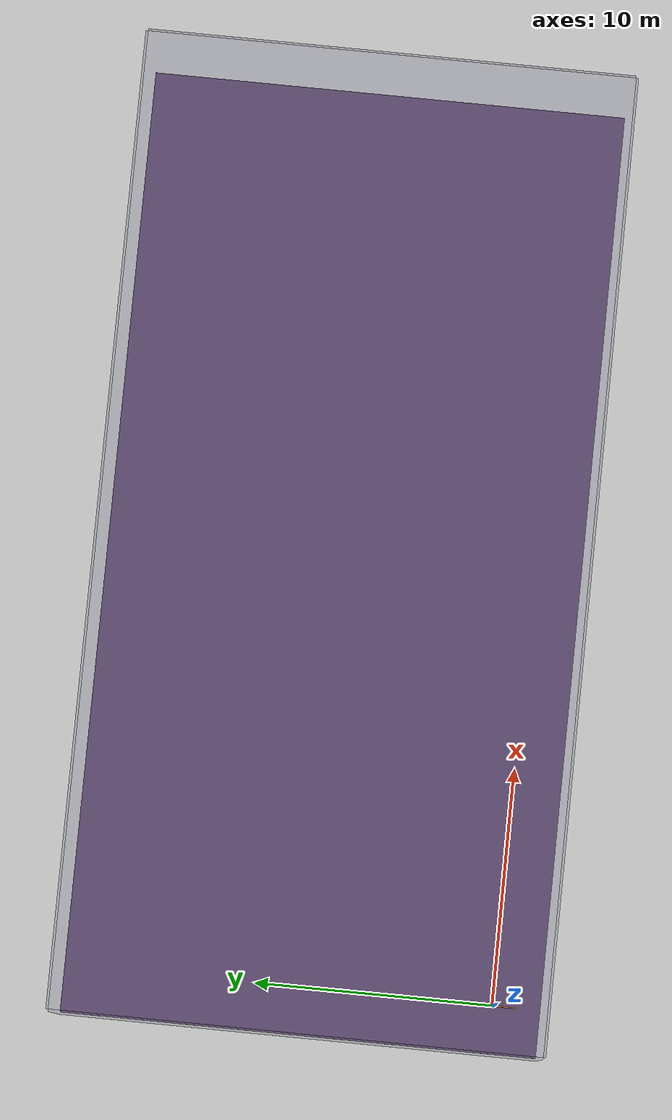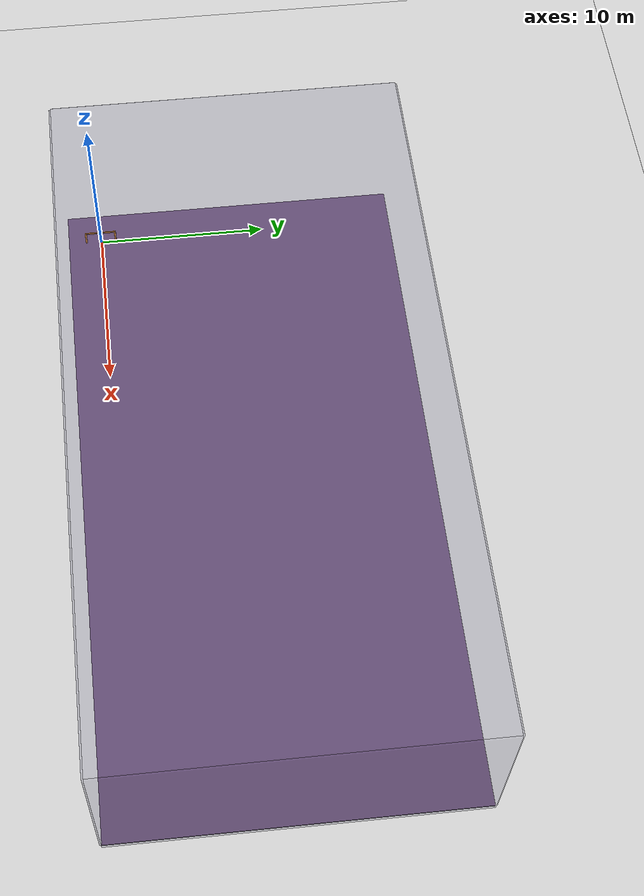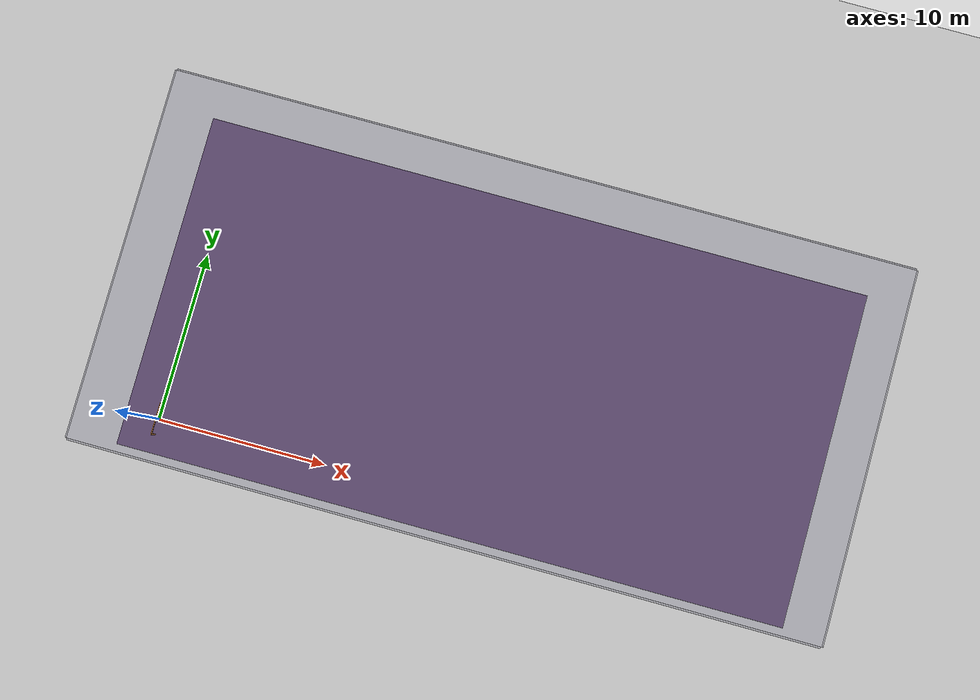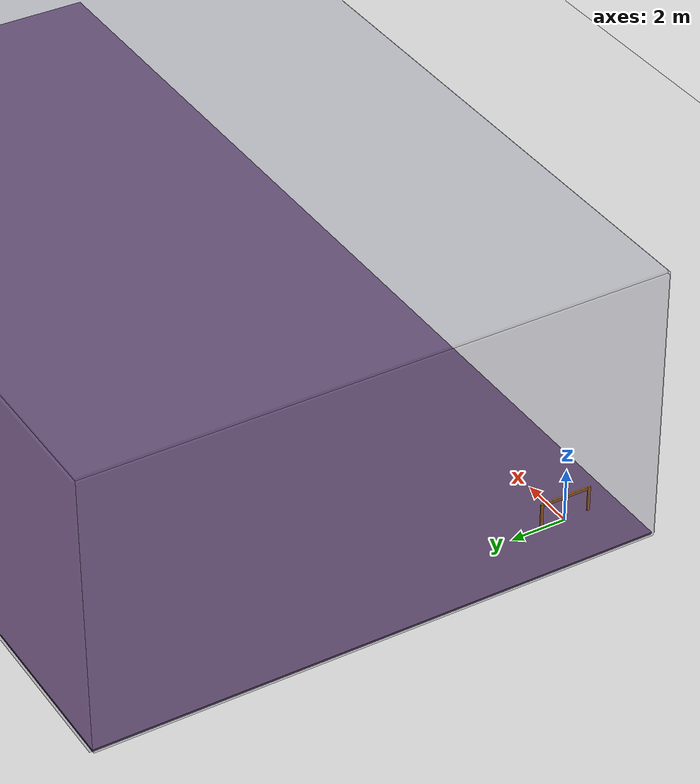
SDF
<?xml version="1.0" ?>
<sdf version="1.4">
  <world name="smart_drone_simple_world">
    <gui>
      <camera name="user_camera">
        <pose>-24. 8. 20. 0. 0.4883 0.</pose>
      </camera>
    </gui>
    <include>
      <uri>model://ground_plane</uri>
    </include>
    <include>
      <uri>model://sun</uri>
    </include>

    <!-- Only one ROS interface plugin is required per world, as any other plugin can connect a Gazebo
         topic to a ROS topic (or vise versa). -->
    <plugin name="ros_interface_plugin" filename="librotors_gazebo_ros_interface_plugin.so"/>

    <spherical_coordinates>
      <surface_model>EARTH_WGS84</surface_model>
      <latitude_deg>47.3667</latitude_deg>
      <longitude_deg>8.5500</longitude_deg>
      <elevation>500.0</elevation>
      <heading_deg>0</heading_deg>
    </spherical_coordinates>
    <physics type='ode'>
      <ode>
        <solver>
          <type>quick</type>
          <iters>1000</iters>
          <sor>1.3</sor>
        </solver>
        <constraints>
          <cfm>0</cfm>
          <erp>0.2</erp>
          <contact_max_correcting_vel>100</contact_max_correcting_vel>
          <contact_surface_layer>0.001</contact_surface_layer>
        </constraints>
      </ode>
      <max_step_size>0.01</max_step_size>
      <real_time_factor>1</real_time_factor>
      <real_time_update_rate>100</real_time_update_rate>
      <gravity>0 0 -9.8</gravity>
    </physics>
    <model name='smart_drone_simple_building'>
      <link name='floor'>
        <pose frame=''>18 8 -0.05 0 -0 0</pose>
        <inertial>
          <mass>1</mass>
          <inertia>
            <ixx>0.166667</ixx>
            <ixy>0</ixy>
            <ixz>0</ixz>
            <iyy>0.166667</iyy>
            <iyz>0</iyz>
            <izz>0.166667</izz>
          </inertia>
          <pose frame=''>0 0 0 0 -0 0</pose>
        </inertial>
        <self_collide>0</self_collide>
        <kinematic>0</kinematic>
        <visual name='visual'>
          <geometry>
            <box>
              <size>40 20 0.2</size>
            </box>
          </geometry>
          <material>
            <script>
              <name>Gazebo/Grey</name>
              <uri>file://media/materials/scripts/gazebo.material</uri>
            </script>
            <shader type='pixel'>
              <normal_map>__default__</normal_map>
            </shader>
            <ambient>0.4 0.3 0.45 1</ambient>
            <diffuse>0.7 0.7 0.7 1</diffuse>
            <specular>0.01 0.01 0.01 1</specular>
            <emissive>0 0 0 1</emissive>
          </material>
          <pose frame=''>0 0 0 0 -0 0</pose>
          <transparency>0</transparency>
          <cast_shadows>1</cast_shadows>
        </visual>
      </link>
      <link name='right_wall'>
        <pose frame=''>18 -2 5 0 -0 0</pose>
        <inertial>
          <mass>1</mass>
          <inertia>
            <ixx>0.166667</ixx>
            <ixy>0</ixy>
            <ixz>0</ixz>
            <iyy>0.166667</iyy>
            <iyz>0</iyz>
            <izz>0.166667</izz>
          </inertia>
          <pose frame=''>0 0 0 0 -0 0</pose>
        </inertial>
        <self_collide>0</self_collide>
        <kinematic>0</kinematic>
        <gravity>1</gravity>
        <visual name='visual'>
          <pose frame=''>0 0 0 0 -0 0</pose>
          <geometry>
            <box>
              <size>40 0.2 10</size>
            </box>
          </geometry>
          <material>
            <lighting>1</lighting>
            <script>
              <uri>file://media/materials/scripts/gazebo.material</uri>
              <name>Gazebo/Grey</name>
            </script>
            <shader type='pixel'>
              <normal_map>__default__</normal_map>
            </shader>
            <ambient>0.3 0.3 0.45 1</ambient>
            <diffuse>0.7 0.7 0.7 1</diffuse>
            <specular>0.01 0.01 0.01 1</specular>
            <emissive>0 0 0 1</emissive>
          </material>
          <transparency>0.95</transparency>
          <cast_shadows>1</cast_shadows>
        </visual>
        <collision name='collision'>
          <laser_retro>0</laser_retro>
          <max_contacts>10</max_contacts>
          <pose frame=''>0 0 0 0 -0 0</pose>
          <geometry>
            <box>
              <size>40 0.2 10</size>
            </box>
          </geometry>
          <surface>
            <friction>
              <ode>
                <mu>1</mu>
                <mu2>1</mu2>
                <fdir1>0 0 0</fdir1>
                <slip1>0</slip1>
                <slip2>0</slip2>
              </ode>
              <torsional>
                <coefficient>1</coefficient>
                <patch_radius>0</patch_radius>
                <surface_radius>0</surface_radius>
                <use_patch_radius>1</use_patch_radius>
                <ode>
                  <slip>0</slip>
                </ode>
              </torsional>
            </friction>
            <bounce>
              <restitution_coefficient>0</restitution_coefficient>
              <threshold>1e+06</threshold>
            </bounce>
            <contact>
              <collide_without_contact>0</collide_without_contact>
              <collide_without_contact_bitmask>1</collide_without_contact_bitmask>
              <collide_bitmask>1</collide_bitmask>
              <ode>
                <soft_cfm>0</soft_cfm>
                <soft_erp>0.2</soft_erp>
                <kp>1e+13</kp>
                <kd>1</kd>
                <max_vel>0.01</max_vel>
                <min_depth>0</min_depth>
              </ode>
              <bullet>
                <split_impulse>1</split_impulse>
                <split_impulse_penetration_threshold>-0.01</split_impulse_penetration_threshold>
                <soft_cfm>0</soft_cfm>
                <soft_erp>0.2</soft_erp>
                <kp>1e+13</kp>
                <kd>1</kd>
              </bullet>
            </contact>
          </surface>
        </collision>
      </link>
      <link name='left_wall'>
        <pose frame=''>18 18 5 0 -0 0</pose>
        <inertial>
          <mass>1</mass>
          <inertia>
            <ixx>0.166667</ixx>
            <ixy>0</ixy>
            <ixz>0</ixz>
            <iyy>0.166667</iyy>
            <iyz>0</iyz>
            <izz>0.166667</izz>
          </inertia>
          <pose frame=''>0 0 0 0 -0 0</pose>
        </inertial>
        <self_collide>0</self_collide>
        <kinematic>0</kinematic>
        <gravity>1</gravity>
        <visual name='visual'>
          <pose frame=''>0 0 0 0 -0 0</pose>
          <geometry>
            <box>
              <size>40 0.2 10</size>
            </box>
          </geometry>
          <material>
            <lighting>1</lighting>
            <script>
              <uri>file://media/materials/scripts/gazebo.material</uri>
              <name>Gazebo/Grey</name>
            </script>
            <shader type='pixel'>
              <normal_map>__default__</normal_map>
            </shader>
            <ambient>0.3 0.3 0.45 1</ambient>
            <diffuse>0.7 0.7 0.7 1</diffuse>
            <specular>0.01 0.01 0.01 1</specular>
            <emissive>0 0 0 1</emissive>
          </material>
          <transparency>0.95</transparency>
          <cast_shadows>1</cast_shadows>
        </visual>
        <collision name='collision'>
          <laser_retro>0</laser_retro>
          <max_contacts>10</max_contacts>
          <pose frame=''>0 0 0 0 -0 0</pose>
          <geometry>
            <box>
              <size>40 0.2 10</size>
            </box>
          </geometry>
          <surface>
            <friction>
              <ode>
                <mu>1</mu>
                <mu2>1</mu2>
                <fdir1>0 0 0</fdir1>
                <slip1>0</slip1>
                <slip2>0</slip2>
              </ode>
              <torsional>
                <coefficient>1</coefficient>
                <patch_radius>0</patch_radius>
                <surface_radius>0</surface_radius>
                <use_patch_radius>1</use_patch_radius>
                <ode>
                  <slip>0</slip>
                </ode>
              </torsional>
            </friction>
            <bounce>
              <restitution_coefficient>0</restitution_coefficient>
              <threshold>1e+06</threshold>
            </bounce>
            <contact>
              <collide_without_contact>0</collide_without_contact>
              <collide_without_contact_bitmask>1</collide_without_contact_bitmask>
              <collide_bitmask>1</collide_bitmask>
              <ode>
                <soft_cfm>0</soft_cfm>
                <soft_erp>0.2</soft_erp>
                <kp>1e+13</kp>
                <kd>1</kd>
                <max_vel>0.01</max_vel>
                <min_depth>0</min_depth>
              </ode>
              <bullet>
                <split_impulse>1</split_impulse>
                <split_impulse_penetration_threshold>-0.01</split_impulse_penetration_threshold>
                <soft_cfm>0</soft_cfm>
                <soft_erp>0.2</soft_erp>
                <kp>1e+13</kp>
                <kd>1</kd>
              </bullet>
            </contact>
          </surface>
        </collision>
      </link>
      <link name='front_wall'>
        <pose frame=''>-2 8 5 0 -0 0</pose>
        <inertial>
          <mass>1</mass>
          <inertia>
            <ixx>0.166667</ixx>
            <ixy>0</ixy>
            <ixz>0</ixz>
            <iyy>0.166667</iyy>
            <iyz>0</iyz>
            <izz>0.166667</izz>
          </inertia>
          <pose frame=''>0 0 0 0 -0 0</pose>
        </inertial>
        <self_collide>0</self_collide>
        <kinematic>0</kinematic>
        <gravity>1</gravity>
        <visual name='visual'>
          <pose frame=''>0 0 0 0 -0 0</pose>
          <geometry>
            <box>
              <size>0.2 20 10</size>
            </box>
          </geometry>
          <material>
            <lighting>1</lighting>
            <script>
              <uri>file://media/materials/scripts/gazebo.material</uri>
              <name>Gazebo/Grey</name>
            </script>
            <shader type='pixel'>
              <normal_map>__default__</normal_map>
            </shader>
            <ambient>0.3 0.3 0.45 1</ambient>
            <diffuse>0.7 0.7 0.7 1</diffuse>
            <specular>0.01 0.01 0.01 1</specular>
            <emissive>0 0 0 1</emissive>
          </material>
          <transparency>0.9</transparency>
          <cast_shadows>1</cast_shadows>
        </visual>
        <collision name='collision'>
          <laser_retro>0</laser_retro>
          <max_contacts>10</max_contacts>
          <pose frame=''>0 0 0 0 -0 0</pose>
          <geometry>
            <box>
              <size>0.2 20 10</size>
            </box>
          </geometry>
          <surface>
            <friction>
              <ode>
                <mu>1</mu>
                <mu2>1</mu2>
                <fdir1>0 0 0</fdir1>
                <slip1>0</slip1>
                <slip2>0</slip2>
              </ode>
              <torsional>
                <coefficient>1</coefficient>
                <patch_radius>0</patch_radius>
                <surface_radius>0</surface_radius>
                <use_patch_radius>1</use_patch_radius>
                <ode>
                  <slip>0</slip>
                </ode>
              </torsional>
            </friction>
            <bounce>
              <restitution_coefficient>0</restitution_coefficient>
              <threshold>1e+06</threshold>
            </bounce>
            <contact>
              <collide_without_contact>0</collide_without_contact>
              <collide_without_contact_bitmask>1</collide_without_contact_bitmask>
              <collide_bitmask>1</collide_bitmask>
              <ode>
                <soft_cfm>0</soft_cfm>
                <soft_erp>0.2</soft_erp>
                <kp>1e+13</kp>
                <kd>1</kd>
                <max_vel>0.01</max_vel>
                <min_depth>0</min_depth>
              </ode>
              <bullet>
                <split_impulse>1</split_impulse>
                <split_impulse_penetration_threshold>-0.01</split_impulse_penetration_threshold>
                <soft_cfm>0</soft_cfm>
                <soft_erp>0.2</soft_erp>
                <kp>1e+13</kp>
                <kd>1</kd>
              </bullet>
            </contact>
          </surface>
        </collision>
      </link>
      <link name='rear_wall'>
        <pose frame=''>38 8 5 0 -0 0</pose>
        <inertial>
          <mass>1</mass>
          <inertia>
            <ixx>0.166667</ixx>
            <ixy>0</ixy>
            <ixz>0</ixz>
            <iyy>0.166667</iyy>
            <iyz>0</iyz>
            <izz>0.166667</izz>
          </inertia>
          <pose frame=''>0 0 0 0 -0 0</pose>
        </inertial>
        <self_collide>0</self_collide>
        <kinematic>0</kinematic>
        <gravity>1</gravity>
        <visual name='visual'>
          <pose frame=''>0 0 0 0 -0 0</pose>
          <geometry>
            <box>
              <size>0.2 20 10</size>
            </box>
          </geometry>
          <material>
            <lighting>1</lighting>
            <script>
              <uri>file://media/materials/scripts/gazebo.material</uri>
              <name>Gazebo/Grey</name>
            </script>
            <shader type='pixel'>
              <normal_map>__default__</normal_map>
            </shader>
            <ambient>0.3 0.3 0.45 1</ambient>
            <diffuse>0.7 0.7 0.7 1</diffuse>
            <specular>0.01 0.01 0.01 1</specular>
            <emissive>0 0 0 1</emissive>
          </material>
          <transparency>0.9</transparency>
          <cast_shadows>1</cast_shadows>
        </visual>
        <collision name='collision'>
          <laser_retro>0</laser_retro>
          <max_contacts>10</max_contacts>
          <pose frame=''>0 0 0 0 -0 0</pose>
          <geometry>
            <box>
              <size>0.2 20 10</size>
            </box>
          </geometry>
          <surface>
            <friction>
              <ode>
                <mu>1</mu>
                <mu2>1</mu2>
                <fdir1>0 0 0</fdir1>
                <slip1>0</slip1>
                <slip2>0</slip2>
              </ode>
              <torsional>
                <coefficient>1</coefficient>
                <patch_radius>0</patch_radius>
                <surface_radius>0</surface_radius>
                <use_patch_radius>1</use_patch_radius>
                <ode>
                  <slip>0</slip>
                </ode>
              </torsional>
            </friction>
            <bounce>
              <restitution_coefficient>0</restitution_coefficient>
              <threshold>1e+06</threshold>
            </bounce>
            <contact>
              <collide_without_contact>0</collide_without_contact>
              <collide_without_contact_bitmask>1</collide_without_contact_bitmask>
              <collide_bitmask>1</collide_bitmask>
              <ode>
                <soft_cfm>0</soft_cfm>
                <soft_erp>0.2</soft_erp>
                <kp>1e+13</kp>
                <kd>1</kd>
                <max_vel>0.01</max_vel>
                <min_depth>0</min_depth>
              </ode>
              <bullet>
                <split_impulse>1</split_impulse>
                <split_impulse_penetration_threshold>-0.01</split_impulse_penetration_threshold>
                <soft_cfm>0</soft_cfm>
                <soft_erp>0.2</soft_erp>
                <kp>1e+13</kp>
                <kd>1</kd>
              </bullet>
            </contact>
          </surface>
        </collision>
      </link>
      <link name='ceiling'>
        <pose frame=''>18 8 10 0 -0 0</pose>
        <inertial>
          <mass>1</mass>
          <inertia>
            <ixx>0.166667</ixx>
            <ixy>0</ixy>
            <ixz>0</ixz>
            <iyy>0.166667</iyy>
            <iyz>0</iyz>
            <izz>0.166667</izz>
          </inertia>
          <pose frame=''>0 0 0 0 -0 0</pose>
        </inertial>
        <self_collide>0</self_collide>
        <kinematic>0</kinematic>
        <gravity>1</gravity>
        <visual name='visual'>
          <pose frame=''>0 0 0 0 -0 0</pose>
          <geometry>
            <box>
              <size>40 20 0.2</size>
            </box>
          </geometry>
          <material>
            <lighting>1</lighting>
            <script>
              <uri>file://media/materials/scripts/gazebo.material</uri>
              <name>Gazebo/Grey</name>
            </script>
            <shader type='pixel'>
              <normal_map>__default__</normal_map>
            </shader>
            <ambient>0.3 0.3 0.45 1</ambient>
            <diffuse>0.7 0.7 0.7 1</diffuse>
            <specular>0.01 0.01 0.01 1</specular>
            <emissive>0 0 0 1</emissive>
          </material>
          <transparency>0.95</transparency>
          <cast_shadows>1</cast_shadows>
        </visual>
        <collision name='collision'>
          <laser_retro>0</laser_retro>
          <max_contacts>10</max_contacts>
          <pose frame=''>0 0 0 0 -0 0</pose>
          <geometry>
            <box>
              <size>40 20 0.2</size>
            </box>
          </geometry>
          <surface>
            <friction>
              <ode>
                <mu>1</mu>
                <mu2>1</mu2>
                <fdir1>0 0 0</fdir1>
                <slip1>0</slip1>
                <slip2>0</slip2>
              </ode>
              <torsional>
                <coefficient>1</coefficient>
                <patch_radius>0</patch_radius>
                <surface_radius>0</surface_radius>
                <use_patch_radius>1</use_patch_radius>
                <ode>
                  <slip>0</slip>
                </ode>
              </torsional>
            </friction>
            <bounce>
              <restitution_coefficient>0</restitution_coefficient>
              <threshold>1e+06</threshold>
            </bounce>
            <contact>
              <collide_without_contact>0</collide_without_contact>
              <collide_without_contact_bitmask>1</collide_without_contact_bitmask>
              <collide_bitmask>1</collide_bitmask>
              <ode>
                <soft_cfm>0</soft_cfm>
                <soft_erp>0.2</soft_erp>
                <kp>1e+13</kp>
                <kd>1</kd>
                <max_vel>0.01</max_vel>
                <min_depth>0</min_depth>
              </ode>
              <bullet>
                <split_impulse>1</split_impulse>
                <split_impulse_penetration_threshold>-0.01</split_impulse_penetration_threshold>
                <soft_cfm>0</soft_cfm>
                <soft_erp>0.2</soft_erp>
                <kp>1e+13</kp>
                <kd>1</kd>
              </bullet>
            </contact>
          </surface>
        </collision>
      </link>
      <static>1</static>
      <allow_auto_disable>1</allow_auto_disable>
    </model>
    <model name='smart_drone_orange_gate0'>
      <link name='left'>
        <pose frame=''>0 -0.9 0 0 -0 0</pose>
        <inertial>
          <mass>1</mass>
          <inertia>
            <ixx>0.166667</ixx>
            <ixy>0</ixy>
            <ixz>0</ixz>
            <iyy>0.166667</iyy>
            <iyz>0</iyz>
            <izz>0.166667</izz>
          </inertia>
          <pose frame=''>0 -0.9 0 0 -0 0</pose>
        </inertial>
        <self_collide>0</self_collide>
        <kinematic>0</kinematic>
        <gravity>1</gravity>
        <visual name='visual'>
          <pose frame=''>0 0 0 0 -0 0</pose>
          <geometry>
            <box>
              <size>0.05 0.1 2</size>
            </box>
          </geometry>
          <material>
            <lighting>1</lighting>
            <script>
              <uri>file://media/materials/scripts/gazebo.material</uri>
              <name>Gazebo/Grey</name>
            </script>
            <shader type='pixel'>
              <normal_map>__default__</normal_map>
            </shader>
            <ambient>0.9 0.54 0.18 1</ambient>
            <diffuse>0.9 0.54 0.18 1</diffuse>
            <specular>0.9 0.54 0.18 1</specular>
            <emissive>0 0 0 1</emissive>
          </material>
          <transparency>0</transparency>
          <cast_shadows>1</cast_shadows>
        </visual>
        <collision name='collision'>
          <laser_retro>0</laser_retro>
          <max_contacts>10</max_contacts>
          <pose frame=''>0 0 0 0 -0 0</pose>
          <geometry>
            <box>
              <size>0.05 0.1 2</size>
            </box>
          </geometry>
          <surface>
            <friction>
              <ode>
                <mu>1</mu>
                <mu2>1</mu2>
                <fdir1>0 0 0</fdir1>
                <slip1>0</slip1>
                <slip2>0</slip2>
              </ode>
              <torsional>
                <coefficient>1</coefficient>
                <patch_radius>0</patch_radius>
                <surface_radius>0</surface_radius>
                <use_patch_radius>1</use_patch_radius>
                <ode>
                  <slip>0</slip>
                </ode>
              </torsional>
            </friction>
            <bounce>
              <restitution_coefficient>0</restitution_coefficient>
              <threshold>1e+06</threshold>
            </bounce>
            <contact>
              <collide_without_contact>0</collide_without_contact>
              <collide_without_contact_bitmask>1</collide_without_contact_bitmask>
              <collide_bitmask>1</collide_bitmask>
              <ode>
                <soft_cfm>0</soft_cfm>
                <soft_erp>0.2</soft_erp>
                <kp>1e+13</kp>
                <kd>1</kd>
                <max_vel>0.01</max_vel>
                <min_depth>0</min_depth>
              </ode>
              <bullet>
                <split_impulse>1</split_impulse>
                <split_impulse_penetration_threshold>-0.01</split_impulse_penetration_threshold>
                <soft_cfm>0</soft_cfm>
                <soft_erp>0.2</soft_erp>
                <kp>1e+13</kp>
                <kd>1</kd>
              </bullet>
            </contact>
          </surface>
        </collision>
      </link>
      <link name='top'>
        <pose frame=''>0 0 0.95 0 -0 0</pose>
        <inertial>
          <mass>1</mass>
          <inertia>
            <ixx>0.166667</ixx>
            <ixy>0</ixy>
            <ixz>0</ixz>
            <iyy>0.166667</iyy>
            <iyz>0</iyz>
            <izz>0.166667</izz>
          </inertia>
          <pose frame=''>0 0 0.95 0 -0 0</pose>
        </inertial>
        <self_collide>0</self_collide>
        <kinematic>0</kinematic>
        <gravity>1</gravity>
        <visual name='visual'>
          <pose frame=''>0 0 0 0 -0 0</pose>
          <geometry>
            <box>
              <size>0.05 1.7 0.1</size>
            </box>
          </geometry>
          <material>
            <lighting>1</lighting>
            <script>
              <uri>file://media/materials/scripts/gazebo.material</uri>
              <name>Gazebo/Grey</name>
            </script>
            <shader type='pixel'>
              <normal_map>__default__</normal_map>
            </shader>
            <ambient>0.9 0.54 0.18 1</ambient>
            <diffuse>0.9 0.54 0.18 1</diffuse>
            <specular>0.9 0.54 0.18 1</specular>
            <emissive>0 0 0 1</emissive>
          </material>
          <transparency>0</transparency>
          <cast_shadows>1</cast_shadows>
        </visual>
        <collision name='collision'>
          <laser_retro>0</laser_retro>
          <max_contacts>10</max_contacts>
          <pose frame=''>0 0 0 0 -0 0</pose>
          <geometry>
            <box>
              <size>0.05 1.7 0.1</size>
            </box>
          </geometry>
          <surface>
            <friction>
              <ode>
                <mu>1</mu>
                <mu2>1</mu2>
                <fdir1>0 0 0</fdir1>
                <slip1>0</slip1>
                <slip2>0</slip2>
              </ode>
              <torsional>
                <coefficient>1</coefficient>
                <patch_radius>0</patch_radius>
                <surface_radius>0</surface_radius>
                <use_patch_radius>1</use_patch_radius>
                <ode>
                  <slip>0</slip>
                </ode>
              </torsional>
            </friction>
            <bounce>
              <restitution_coefficient>0</restitution_coefficient>
              <threshold>1e+06</threshold>
            </bounce>
            <contact>
              <collide_without_contact>0</collide_without_contact>
              <collide_without_contact_bitmask>1</collide_without_contact_bitmask>
              <collide_bitmask>1</collide_bitmask>
              <ode>
                <soft_cfm>0</soft_cfm>
                <soft_erp>0.2</soft_erp>
                <kp>1e+13</kp>
                <kd>1</kd>
                <max_vel>0.01</max_vel>
                <min_depth>0</min_depth>
              </ode>
              <bullet>
                <split_impulse>1</split_impulse>
                <split_impulse_penetration_threshold>-0.01</split_impulse_penetration_threshold>
                <soft_cfm>0</soft_cfm>
                <soft_erp>0.2</soft_erp>
                <kp>1e+13</kp>
                <kd>1</kd>
              </bullet>
            </contact>
          </surface>
        </collision>
      </link>
      <link name='bot'>
        <pose frame=''>0 0 -0.95 0 -0 0</pose>
        <inertial>
          <mass>1</mass>
          <inertia>
            <ixx>0.166667</ixx>
            <ixy>0</ixy>
            <ixz>0</ixz>
            <iyy>0.166667</iyy>
            <iyz>0</iyz>
            <izz>0.166667</izz>
          </inertia>
          <pose frame=''>0 0 -0.95 0 -0 0</pose>
        </inertial>
        <self_collide>0</self_collide>
        <kinematic>0</kinematic>
        <gravity>1</gravity>
        <visual name='visual'>
          <pose frame=''>0 0 0 0 -0 0</pose>
          <geometry>
            <box>
              <size>0.05 1.7 0.1</size>
            </box>
          </geometry>
          <material>
            <lighting>1</lighting>
            <script>
              <uri>file://media/materials/scripts/gazebo.material</uri>
              <name>Gazebo/Grey</name>
            </script>
            <shader type='pixel'>
              <normal_map>__default__</normal_map>
            </shader>
            <ambient>0.9 0.54 0.18 1</ambient>
            <diffuse>0.9 0.54 0.18 1</diffuse>
            <specular>0.9 0.54 0.18 1</specular>
            <emissive>0 0 0 1</emissive>
          </material>
          <transparency>0</transparency>
          <cast_shadows>1</cast_shadows>
        </visual>
        <collision name='collision'>
          <laser_retro>0</laser_retro>
          <max_contacts>10</max_contacts>
          <pose frame=''>0 0 0 0 -0 0</pose>
          <geometry>
            <box>
              <size>0.05 1.7 0.1</size>
            </box>
          </geometry>
          <surface>
            <friction>
              <ode>
                <mu>1</mu>
                <mu2>1</mu2>
                <fdir1>0 0 0</fdir1>
                <slip1>0</slip1>
                <slip2>0</slip2>
              </ode>
              <torsional>
                <coefficient>1</coefficient>
                <patch_radius>0</patch_radius>
                <surface_radius>0</surface_radius>
                <use_patch_radius>1</use_patch_radius>
                <ode>
                  <slip>0</slip>
                </ode>
              </torsional>
            </friction>
            <bounce>
              <restitution_coefficient>0</restitution_coefficient>
              <threshold>1e+06</threshold>
            </bounce>
            <contact>
              <collide_without_contact>0</collide_without_contact>
              <collide_without_contact_bitmask>1</collide_without_contact_bitmask>
              <collide_bitmask>1</collide_bitmask>
              <ode>
                <soft_cfm>0</soft_cfm>
                <soft_erp>0.2</soft_erp>
                <kp>1e+13</kp>
                <kd>1</kd>
                <max_vel>0.01</max_vel>
                <min_depth>0</min_depth>
              </ode>
              <bullet>
                <split_impulse>1</split_impulse>
                <split_impulse_penetration_threshold>-0.01</split_impulse_penetration_threshold>
                <soft_cfm>0</soft_cfm>
                <soft_erp>0.2</soft_erp>
                <kp>1e+13</kp>
                <kd>1</kd>
              </bullet>
            </contact>
          </surface>
        </collision>
      </link>
      <link name='right'>
        <pose frame=''>0 0.9 0 0 -0 0</pose>
        <inertial>
          <mass>1</mass>
          <inertia>
            <ixx>0.166667</ixx>
            <ixy>0</ixy>
            <ixz>0</ixz>
            <iyy>0.166667</iyy>
            <iyz>0</iyz>
            <izz>0.166667</izz>
          </inertia>
          <pose frame=''>0 0.9 0 0 -0 0</pose>
        </inertial>
        <self_collide>0</self_collide>
        <kinematic>0</kinematic>
        <gravity>1</gravity>
        <visual name='visual'>
          <pose frame=''>0 0 0 0 -0 0</pose>
          <geometry>
            <box>
              <size>0.05 0.1 2</size>
            </box>
          </geometry>
          <material>
            <lighting>1</lighting>
            <script>
              <uri>file://media/materials/scripts/gazebo.material</uri>
              <name>Gazebo/Grey</name>
            </script>
            <shader type='pixel'>
              <normal_map>__default__</normal_map>
            </shader>
            <ambient>0.9 0.54 0.18 1</ambient>
            <diffuse>0.9 0.54 0.18 1</diffuse>
            <specular>0.9 0.54 0.18 1</specular>
            <emissive>0 0 0 1</emissive>
          </material>
          <transparency>0</transparency>
          <cast_shadows>1</cast_shadows>
        </visual>
        <collision name='collision'>
          <laser_retro>0</laser_retro>
          <max_contacts>10</max_contacts>
          <pose frame=''>0 0 0 0 -0 0</pose>
          <geometry>
            <box>
              <size>0.05 0.1 2</size>
            </box>
          </geometry>
          <surface>
            <friction>
              <ode>
                <mu>1</mu>
                <mu2>1</mu2>
                <fdir1>0 0 0</fdir1>
                <slip1>0</slip1>
                <slip2>0</slip2>
              </ode>
              <torsional>
                <coefficient>1</coefficient>
                <patch_radius>0</patch_radius>
                <surface_radius>0</surface_radius>
                <use_patch_radius>1</use_patch_radius>
                <ode>
                  <slip>0</slip>
                </ode>
              </torsional>
            </friction>
            <bounce>
              <restitution_coefficient>0</restitution_coefficient>
              <threshold>1e+06</threshold>
            </bounce>
            <contact>
              <collide_without_contact>0</collide_without_contact>
              <collide_without_contact_bitmask>1</collide_without_contact_bitmask>
              <collide_bitmask>1</collide_bitmask>
              <ode>
                <soft_cfm>0</soft_cfm>
                <soft_erp>0.2</soft_erp>
                <kp>1e+13</kp>
                <kd>1</kd>
                <max_vel>0.01</max_vel>
                <min_depth>0</min_depth>
              </ode>
              <bullet>
                <split_impulse>1</split_impulse>
                <split_impulse_penetration_threshold>-0.01</split_impulse_penetration_threshold>
                <soft_cfm>0</soft_cfm>
                <soft_erp>0.2</soft_erp>
                <kp>1e+13</kp>
                <kd>1</kd>
              </bullet>
            </contact>
          </surface>
        </collision>
      </link>
      <static>1</static>
      <allow_auto_disable>1</allow_auto_disable>
    </model>
    <model name='smart_drone_orange_gate1'>
      <link name='left'>
        <pose frame=''>0 -0.9 0 0 -0 0</pose>
        <inertial>
          <mass>1</mass>
          <inertia>
            <ixx>0.166667</ixx>
            <ixy>0</ixy>
            <ixz>0</ixz>
            <iyy>0.166667</iyy>
            <iyz>0</iyz>
            <izz>0.166667</izz>
          </inertia>
          <pose frame=''>0 -0.9 0 0 -0 0</pose>
        </inertial>
        <self_collide>0</self_collide>
        <kinematic>0</kinematic>
        <gravity>1</gravity>
        <visual name='visual'>
          <pose frame=''>0 0 0 0 -0 0</pose>
          <geometry>
            <box>
              <size>0.05 0.1 2</size>
            </box>
          </geometry>
          <material>
            <lighting>1</lighting>
            <script>
              <uri>file://media/materials/scripts/gazebo.material</uri>
              <name>Gazebo/Grey</name>
            </script>
            <shader type='pixel'>
              <normal_map>__default__</normal_map>
            </shader>
            <ambient>0.9 0.54 0.18 1</ambient>
            <diffuse>0.9 0.54 0.18 1</diffuse>
            <specular>0.9 0.54 0.18 1</specular>
            <emissive>0 0 0 1</emissive>
          </material>
          <transparency>0</transparency>
          <cast_shadows>1</cast_shadows>
        </visual>
        <collision name='collision'>
          <laser_retro>0</laser_retro>
          <max_contacts>10</max_contacts>
          <pose frame=''>0 0 0 0 -0 0</pose>
          <geometry>
            <box>
              <size>0.05 0.1 2</size>
            </box>
          </geometry>
          <surface>
            <friction>
              <ode>
                <mu>1</mu>
                <mu2>1</mu2>
                <fdir1>0 0 0</fdir1>
                <slip1>0</slip1>
                <slip2>0</slip2>
              </ode>
              <torsional>
                <coefficient>1</coefficient>
                <patch_radius>0</patch_radius>
                <surface_radius>0</surface_radius>
                <use_patch_radius>1</use_patch_radius>
                <ode>
                  <slip>0</slip>
                </ode>
              </torsional>
            </friction>
            <bounce>
              <restitution_coefficient>0</restitution_coefficient>
              <threshold>1e+06</threshold>
            </bounce>
            <contact>
              <collide_without_contact>0</collide_without_contact>
              <collide_without_contact_bitmask>1</collide_without_contact_bitmask>
              <collide_bitmask>1</collide_bitmask>
              <ode>
                <soft_cfm>0</soft_cfm>
                <soft_erp>0.2</soft_erp>
                <kp>1e+13</kp>
                <kd>1</kd>
                <max_vel>0.01</max_vel>
                <min_depth>0</min_depth>
              </ode>
              <bullet>
                <split_impulse>1</split_impulse>
                <split_impulse_penetration_threshold>-0.01</split_impulse_penetration_threshold>
                <soft_cfm>0</soft_cfm>
                <soft_erp>0.2</soft_erp>
                <kp>1e+13</kp>
                <kd>1</kd>
              </bullet>
            </contact>
          </surface>
        </collision>
      </link>
      <link name='top'>
        <pose frame=''>0 0 0.95 0 -0 0</pose>
        <inertial>
          <mass>1</mass>
          <inertia>
            <ixx>0.166667</ixx>
            <ixy>0</ixy>
            <ixz>0</ixz>
            <iyy>0.166667</iyy>
            <iyz>0</iyz>
            <izz>0.166667</izz>
          </inertia>
          <pose frame=''>0 0 0.95 0 -0 0</pose>
        </inertial>
        <self_collide>0</self_collide>
        <kinematic>0</kinematic>
        <gravity>1</gravity>
        <visual name='visual'>
          <pose frame=''>0 0 0 0 -0 0</pose>
          <geometry>
            <box>
              <size>0.05 1.7 0.1</size>
            </box>
          </geometry>
          <material>
            <lighting>1</lighting>
            <script>
              <uri>file://media/materials/scripts/gazebo.material</uri>
              <name>Gazebo/Grey</name>
            </script>
            <shader type='pixel'>
              <normal_map>__default__</normal_map>
            </shader>
            <ambient>0.9 0.54 0.18 1</ambient>
            <diffuse>0.9 0.54 0.18 1</diffuse>
            <specular>0.9 0.54 0.18 1</specular>
            <emissive>0 0 0 1</emissive>
          </material>
          <transparency>0</transparency>
          <cast_shadows>1</cast_shadows>
        </visual>
        <collision name='collision'>
          <laser_retro>0</laser_retro>
          <max_contacts>10</max_contacts>
          <pose frame=''>0 0 0 0 -0 0</pose>
          <geometry>
            <box>
              <size>0.05 1.7 0.1</size>
            </box>
          </geometry>
          <surface>
            <friction>
              <ode>
                <mu>1</mu>
                <mu2>1</mu2>
                <fdir1>0 0 0</fdir1>
                <slip1>0</slip1>
                <slip2>0</slip2>
              </ode>
              <torsional>
                <coefficient>1</coefficient>
                <patch_radius>0</patch_radius>
                <surface_radius>0</surface_radius>
                <use_patch_radius>1</use_patch_radius>
                <ode>
                  <slip>0</slip>
                </ode>
              </torsional>
            </friction>
            <bounce>
              <restitution_coefficient>0</restitution_coefficient>
              <threshold>1e+06</threshold>
            </bounce>
            <contact>
              <collide_without_contact>0</collide_without_contact>
              <collide_without_contact_bitmask>1</collide_without_contact_bitmask>
              <collide_bitmask>1</collide_bitmask>
              <ode>
                <soft_cfm>0</soft_cfm>
                <soft_erp>0.2</soft_erp>
                <kp>1e+13</kp>
                <kd>1</kd>
                <max_vel>0.01</max_vel>
                <min_depth>0</min_depth>
              </ode>
              <bullet>
                <split_impulse>1</split_impulse>
                <split_impulse_penetration_threshold>-0.01</split_impulse_penetration_threshold>
                <soft_cfm>0</soft_cfm>
                <soft_erp>0.2</soft_erp>
                <kp>1e+13</kp>
                <kd>1</kd>
              </bullet>
            </contact>
          </surface>
        </collision>
      </link>
      <link name='bot'>
        <pose frame=''>0 0 -0.95 0 -0 0</pose>
        <inertial>
          <mass>1</mass>
          <inertia>
            <ixx>0.166667</ixx>
            <ixy>0</ixy>
            <ixz>0</ixz>
            <iyy>0.166667</iyy>
            <iyz>0</iyz>
            <izz>0.166667</izz>
          </inertia>
          <pose frame=''>0 0 -0.95 0 -0 0</pose>
        </inertial>
        <self_collide>0</self_collide>
        <kinematic>0</kinematic>
        <gravity>1</gravity>
        <visual name='visual'>
          <pose frame=''>0 0 0 0 -0 0</pose>
          <geometry>
            <box>
              <size>0.05 1.7 0.1</size>
            </box>
          </geometry>
          <material>
            <lighting>1</lighting>
            <script>
              <uri>file://media/materials/scripts/gazebo.material</uri>
              <name>Gazebo/Grey</name>
            </script>
            <shader type='pixel'>
              <normal_map>__default__</normal_map>
            </shader>
            <ambient>0.9 0.54 0.18 1</ambient>
            <diffuse>0.9 0.54 0.18 1</diffuse>
            <specular>0.9 0.54 0.18 1</specular>
            <emissive>0 0 0 1</emissive>
          </material>
          <transparency>0</transparency>
          <cast_shadows>1</cast_shadows>
        </visual>
        <collision name='collision'>
          <laser_retro>0</laser_retro>
          <max_contacts>10</max_contacts>
          <pose frame=''>0 0 0 0 -0 0</pose>
          <geometry>
            <box>
              <size>0.05 1.7 0.1</size>
            </box>
          </geometry>
          <surface>
            <friction>
              <ode>
                <mu>1</mu>
                <mu2>1</mu2>
                <fdir1>0 0 0</fdir1>
                <slip1>0</slip1>
                <slip2>0</slip2>
              </ode>
              <torsional>
                <coefficient>1</coefficient>
                <patch_radius>0</patch_radius>
                <surface_radius>0</surface_radius>
                <use_patch_radius>1</use_patch_radius>
                <ode>
                  <slip>0</slip>
                </ode>
              </torsional>
            </friction>
            <bounce>
              <restitution_coefficient>0</restitution_coefficient>
              <threshold>1e+06</threshold>
            </bounce>
            <contact>
              <collide_without_contact>0</collide_without_contact>
              <collide_without_contact_bitmask>1</collide_without_contact_bitmask>
              <collide_bitmask>1</collide_bitmask>
              <ode>
                <soft_cfm>0</soft_cfm>
                <soft_erp>0.2</soft_erp>
                <kp>1e+13</kp>
                <kd>1</kd>
                <max_vel>0.01</max_vel>
                <min_depth>0</min_depth>
              </ode>
              <bullet>
                <split_impulse>1</split_impulse>
                <split_impulse_penetration_threshold>-0.01</split_impulse_penetration_threshold>
                <soft_cfm>0</soft_cfm>
                <soft_erp>0.2</soft_erp>
                <kp>1e+13</kp>
                <kd>1</kd>
              </bullet>
            </contact>
          </surface>
        </collision>
      </link>
      <link name='right'>
        <pose frame=''>0 0.9 0 0 -0 0</pose>
        <inertial>
          <mass>1</mass>
          <inertia>
            <ixx>0.166667</ixx>
            <ixy>0</ixy>
            <ixz>0</ixz>
            <iyy>0.166667</iyy>
            <iyz>0</iyz>
            <izz>0.166667</izz>
          </inertia>
          <pose frame=''>0 0.9 0 0 -0 0</pose>
        </inertial>
        <self_collide>0</self_collide>
        <kinematic>0</kinematic>
        <gravity>1</gravity>
        <visual name='visual'>
          <pose frame=''>0 0 0 0 -0 0</pose>
          <geometry>
            <box>
              <size>0.05 0.1 2</size>
            </box>
          </geometry>
          <material>
            <lighting>1</lighting>
            <script>
              <uri>file://media/materials/scripts/gazebo.material</uri>
              <name>Gazebo/Grey</name>
            </script>
            <shader type='pixel'>
              <normal_map>__default__</normal_map>
            </shader>
            <ambient>0.9 0.54 0.18 1</ambient>
            <diffuse>0.9 0.54 0.18 1</diffuse>
            <specular>0.9 0.54 0.18 1</specular>
            <emissive>0 0 0 1</emissive>
          </material>
          <transparency>0</transparency>
          <cast_shadows>1</cast_shadows>
        </visual>
        <collision name='collision'>
          <laser_retro>0</laser_retro>
          <max_contacts>10</max_contacts>
          <pose frame=''>0 0 0 0 -0 0</pose>
          <geometry>
            <box>
              <size>0.05 0.1 2</size>
            </box>
          </geometry>
          <surface>
            <friction>
              <ode>
                <mu>1</mu>
                <mu2>1</mu2>
                <fdir1>0 0 0</fdir1>
                <slip1>0</slip1>
                <slip2>0</slip2>
              </ode>
              <torsional>
                <coefficient>1</coefficient>
                <patch_radius>0</patch_radius>
                <surface_radius>0</surface_radius>
                <use_patch_radius>1</use_patch_radius>
                <ode>
                  <slip>0</slip>
                </ode>
              </torsional>
            </friction>
            <bounce>
              <restitution_coefficient>0</restitution_coefficient>
              <threshold>1e+06</threshold>
            </bounce>
            <contact>
              <collide_without_contact>0</collide_without_contact>
              <collide_without_contact_bitmask>1</collide_without_contact_bitmask>
              <collide_bitmask>1</collide_bitmask>
              <ode>
                <soft_cfm>0</soft_cfm>
                <soft_erp>0.2</soft_erp>
                <kp>1e+13</kp>
                <kd>1</kd>
                <max_vel>0.01</max_vel>
                <min_depth>0</min_depth>
              </ode>
              <bullet>
                <split_impulse>1</split_impulse>
                <split_impulse_penetration_threshold>-0.01</split_impulse_penetration_threshold>
                <soft_cfm>0</soft_cfm>
                <soft_erp>0.2</soft_erp>
                <kp>1e+13</kp>
                <kd>1</kd>
              </bullet>
            </contact>
          </surface>
        </collision>
      </link>
      <static>1</static>
      <allow_auto_disable>1</allow_auto_disable>
    </model>
    <model name='smart_drone_orange_gate2'>
      <link name='left'>
        <pose frame=''>0 -0.9 0 0 -0 0</pose>
        <inertial>
          <mass>1</mass>
          <inertia>
            <ixx>0.166667</ixx>
            <ixy>0</ixy>
            <ixz>0</ixz>
            <iyy>0.166667</iyy>
            <iyz>0</iyz>
            <izz>0.166667</izz>
          </inertia>
          <pose frame=''>0 -0.9 0 0 -0 0</pose>
        </inertial>
        <self_collide>0</self_collide>
        <kinematic>0</kinematic>
        <gravity>1</gravity>
        <visual name='visual'>
          <pose frame=''>0 0 0 0 -0 0</pose>
          <geometry>
            <box>
              <size>0.05 0.1 2</size>
            </box>
          </geometry>
          <material>
            <lighting>1</lighting>
            <script>
              <uri>file://media/materials/scripts/gazebo.material</uri>
              <name>Gazebo/Grey</name>
            </script>
            <shader type='pixel'>
              <normal_map>__default__</normal_map>
            </shader>
            <ambient>0.9 0.54 0.18 1</ambient>
            <diffuse>0.9 0.54 0.18 1</diffuse>
            <specular>0.9 0.54 0.18 1</specular>
            <emissive>0 0 0 1</emissive>
          </material>
          <transparency>0</transparency>
          <cast_shadows>1</cast_shadows>
        </visual>
        <collision name='collision'>
          <laser_retro>0</laser_retro>
          <max_contacts>10</max_contacts>
          <pose frame=''>0 0 0 0 -0 0</pose>
          <geometry>
            <box>
              <size>0.05 0.1 2</size>
            </box>
          </geometry>
          <surface>
            <friction>
              <ode>
                <mu>1</mu>
                <mu2>1</mu2>
                <fdir1>0 0 0</fdir1>
                <slip1>0</slip1>
                <slip2>0</slip2>
              </ode>
              <torsional>
                <coefficient>1</coefficient>
                <patch_radius>0</patch_radius>
                <surface_radius>0</surface_radius>
                <use_patch_radius>1</use_patch_radius>
                <ode>
                  <slip>0</slip>
                </ode>
              </torsional>
            </friction>
            <bounce>
              <restitution_coefficient>0</restitution_coefficient>
              <threshold>1e+06</threshold>
            </bounce>
            <contact>
              <collide_without_contact>0</collide_without_contact>
              <collide_without_contact_bitmask>1</collide_without_contact_bitmask>
              <collide_bitmask>1</collide_bitmask>
              <ode>
                <soft_cfm>0</soft_cfm>
                <soft_erp>0.2</soft_erp>
                <kp>1e+13</kp>
                <kd>1</kd>
                <max_vel>0.01</max_vel>
                <min_depth>0</min_depth>
              </ode>
              <bullet>
                <split_impulse>1</split_impulse>
                <split_impulse_penetration_threshold>-0.01</split_impulse_penetration_threshold>
                <soft_cfm>0</soft_cfm>
                <soft_erp>0.2</soft_erp>
                <kp>1e+13</kp>
                <kd>1</kd>
              </bullet>
            </contact>
          </surface>
        </collision>
      </link>
      <link name='top'>
        <pose frame=''>0 0 0.95 0 -0 0</pose>
        <inertial>
          <mass>1</mass>
          <inertia>
            <ixx>0.166667</ixx>
            <ixy>0</ixy>
            <ixz>0</ixz>
            <iyy>0.166667</iyy>
            <iyz>0</iyz>
            <izz>0.166667</izz>
          </inertia>
          <pose frame=''>0 0 0.95 0 -0 0</pose>
        </inertial>
        <self_collide>0</self_collide>
        <kinematic>0</kinematic>
        <gravity>1</gravity>
        <visual name='visual'>
          <pose frame=''>0 0 0 0 -0 0</pose>
          <geometry>
            <box>
              <size>0.05 1.7 0.1</size>
            </box>
          </geometry>
          <material>
            <lighting>1</lighting>
            <script>
              <uri>file://media/materials/scripts/gazebo.material</uri>
              <name>Gazebo/Grey</name>
            </script>
            <shader type='pixel'>
              <normal_map>__default__</normal_map>
            </shader>
            <ambient>0.9 0.54 0.18 1</ambient>
            <diffuse>0.9 0.54 0.18 1</diffuse>
            <specular>0.9 0.54 0.18 1</specular>
            <emissive>0 0 0 1</emissive>
          </material>
          <transparency>0</transparency>
          <cast_shadows>1</cast_shadows>
        </visual>
        <collision name='collision'>
          <laser_retro>0</laser_retro>
          <max_contacts>10</max_contacts>
          <pose frame=''>0 0 0 0 -0 0</pose>
          <geometry>
            <box>
              <size>0.05 1.7 0.1</size>
            </box>
          </geometry>
          <surface>
            <friction>
              <ode>
                <mu>1</mu>
                <mu2>1</mu2>
                <fdir1>0 0 0</fdir1>
                <slip1>0</slip1>
                <slip2>0</slip2>
              </ode>
              <torsional>
                <coefficient>1</coefficient>
                <patch_radius>0</patch_radius>
                <surface_radius>0</surface_radius>
                <use_patch_radius>1</use_patch_radius>
                <ode>
                  <slip>0</slip>
                </ode>
              </torsional>
            </friction>
            <bounce>
              <restitution_coefficient>0</restitution_coefficient>
              <threshold>1e+06</threshold>
            </bounce>
            <contact>
              <collide_without_contact>0</collide_without_contact>
              <collide_without_contact_bitmask>1</collide_without_contact_bitmask>
              <collide_bitmask>1</collide_bitmask>
              <ode>
                <soft_cfm>0</soft_cfm>
                <soft_erp>0.2</soft_erp>
                <kp>1e+13</kp>
                <kd>1</kd>
                <max_vel>0.01</max_vel>
                <min_depth>0</min_depth>
              </ode>
              <bullet>
                <split_impulse>1</split_impulse>
                <split_impulse_penetration_threshold>-0.01</split_impulse_penetration_threshold>
                <soft_cfm>0</soft_cfm>
                <soft_erp>0.2</soft_erp>
                <kp>1e+13</kp>
                <kd>1</kd>
              </bullet>
            </contact>
          </surface>
        </collision>
      </link>
      <link name='bot'>
        <pose frame=''>0 0 -0.95 0 -0 0</pose>
        <inertial>
          <mass>1</mass>
          <inertia>
            <ixx>0.166667</ixx>
            <ixy>0</ixy>
            <ixz>0</ixz>
            <iyy>0.166667</iyy>
            <iyz>0</iyz>
            <izz>0.166667</izz>
          </inertia>
          <pose frame=''>0 0 -0.95 0 -0 0</pose>
        </inertial>
        <self_collide>0</self_collide>
        <kinematic>0</kinematic>
        <gravity>1</gravity>
        <visual name='visual'>
          <pose frame=''>0 0 0 0 -0 0</pose>
          <geometry>
            <box>
              <size>0.05 1.7 0.1</size>
            </box>
          </geometry>
          <material>
            <lighting>1</lighting>
            <script>
              <uri>file://media/materials/scripts/gazebo.material</uri>
              <name>Gazebo/Grey</name>
            </script>
            <shader type='pixel'>
              <normal_map>__default__</normal_map>
            </shader>
            <ambient>0.9 0.54 0.18 1</ambient>
            <diffuse>0.9 0.54 0.18 1</diffuse>
            <specular>0.9 0.54 0.18 1</specular>
            <emissive>0 0 0 1</emissive>
          </material>
          <transparency>0</transparency>
          <cast_shadows>1</cast_shadows>
        </visual>
        <collision name='collision'>
          <laser_retro>0</laser_retro>
          <max_contacts>10</max_contacts>
          <pose frame=''>0 0 0 0 -0 0</pose>
          <geometry>
            <box>
              <size>0.05 1.7 0.1</size>
            </box>
          </geometry>
          <surface>
            <friction>
              <ode>
                <mu>1</mu>
                <mu2>1</mu2>
                <fdir1>0 0 0</fdir1>
                <slip1>0</slip1>
                <slip2>0</slip2>
              </ode>
              <torsional>
                <coefficient>1</coefficient>
                <patch_radius>0</patch_radius>
                <surface_radius>0</surface_radius>
                <use_patch_radius>1</use_patch_radius>
                <ode>
                  <slip>0</slip>
                </ode>
              </torsional>
            </friction>
            <bounce>
              <restitution_coefficient>0</restitution_coefficient>
              <threshold>1e+06</threshold>
            </bounce>
            <contact>
              <collide_without_contact>0</collide_without_contact>
              <collide_without_contact_bitmask>1</collide_without_contact_bitmask>
              <collide_bitmask>1</collide_bitmask>
              <ode>
                <soft_cfm>0</soft_cfm>
                <soft_erp>0.2</soft_erp>
                <kp>1e+13</kp>
                <kd>1</kd>
                <max_vel>0.01</max_vel>
                <min_depth>0</min_depth>
              </ode>
              <bullet>
                <split_impulse>1</split_impulse>
                <split_impulse_penetration_threshold>-0.01</split_impulse_penetration_threshold>
                <soft_cfm>0</soft_cfm>
                <soft_erp>0.2</soft_erp>
                <kp>1e+13</kp>
                <kd>1</kd>
              </bullet>
            </contact>
          </surface>
        </collision>
      </link>
      <link name='right'>
        <pose frame=''>0 0.9 0 0 -0 0</pose>
        <inertial>
          <mass>1</mass>
          <inertia>
            <ixx>0.166667</ixx>
            <ixy>0</ixy>
            <ixz>0</ixz>
            <iyy>0.166667</iyy>
            <iyz>0</iyz>
            <izz>0.166667</izz>
          </inertia>
          <pose frame=''>0 0.9 0 0 -0 0</pose>
        </inertial>
        <self_collide>0</self_collide>
        <kinematic>0</kinematic>
        <gravity>1</gravity>
        <visual name='visual'>
          <pose frame=''>0 0 0 0 -0 0</pose>
          <geometry>
            <box>
              <size>0.05 0.1 2</size>
            </box>
          </geometry>
          <material>
            <lighting>1</lighting>
            <script>
              <uri>file://media/materials/scripts/gazebo.material</uri>
              <name>Gazebo/Grey</name>
            </script>
            <shader type='pixel'>
              <normal_map>__default__</normal_map>
            </shader>
            <ambient>0.9 0.54 0.18 1</ambient>
            <diffuse>0.9 0.54 0.18 1</diffuse>
            <specular>0.9 0.54 0.18 1</specular>
            <emissive>0 0 0 1</emissive>
          </material>
          <transparency>0</transparency>
          <cast_shadows>1</cast_shadows>
        </visual>
        <collision name='collision'>
          <laser_retro>0</laser_retro>
          <max_contacts>10</max_contacts>
          <pose frame=''>0 0 0 0 -0 0</pose>
          <geometry>
            <box>
              <size>0.05 0.1 2</size>
            </box>
          </geometry>
          <surface>
            <friction>
              <ode>
                <mu>1</mu>
                <mu2>1</mu2>
                <fdir1>0 0 0</fdir1>
                <slip1>0</slip1>
                <slip2>0</slip2>
              </ode>
              <torsional>
                <coefficient>1</coefficient>
                <patch_radius>0</patch_radius>
                <surface_radius>0</surface_radius>
                <use_patch_radius>1</use_patch_radius>
                <ode>
                  <slip>0</slip>
                </ode>
              </torsional>
            </friction>
            <bounce>
              <restitution_coefficient>0</restitution_coefficient>
              <threshold>1e+06</threshold>
            </bounce>
            <contact>
              <collide_without_contact>0</collide_without_contact>
              <collide_without_contact_bitmask>1</collide_without_contact_bitmask>
              <collide_bitmask>1</collide_bitmask>
              <ode>
                <soft_cfm>0</soft_cfm>
                <soft_erp>0.2</soft_erp>
                <kp>1e+13</kp>
                <kd>1</kd>
                <max_vel>0.01</max_vel>
                <min_depth>0</min_depth>
              </ode>
              <bullet>
                <split_impulse>1</split_impulse>
                <split_impulse_penetration_threshold>-0.01</split_impulse_penetration_threshold>
                <soft_cfm>0</soft_cfm>
                <soft_erp>0.2</soft_erp>
                <kp>1e+13</kp>
                <kd>1</kd>
              </bullet>
            </contact>
          </surface>
        </collision>
      </link>
      <static>1</static>
      <allow_auto_disable>1</allow_auto_disable>
    </model>
    <model name='smart_drone_orange_gate3'>
      <link name='left'>
        <pose frame=''>0 -0.9 0 0 -0 0</pose>
        <inertial>
          <mass>1</mass>
          <inertia>
            <ixx>0.166667</ixx>
            <ixy>0</ixy>
            <ixz>0</ixz>
            <iyy>0.166667</iyy>
            <iyz>0</iyz>
            <izz>0.166667</izz>
          </inertia>
          <pose frame=''>0 -0.9 0 0 -0 0</pose>
        </inertial>
        <self_collide>0</self_collide>
        <kinematic>0</kinematic>
        <gravity>1</gravity>
        <visual name='visual'>
          <pose frame=''>0 0 0 0 -0 0</pose>
          <geometry>
            <box>
              <size>0.05 0.1 2</size>
            </box>
          </geometry>
          <material>
            <lighting>1</lighting>
            <script>
              <uri>file://media/materials/scripts/gazebo.material</uri>
              <name>Gazebo/Grey</name>
            </script>
            <shader type='pixel'>
              <normal_map>__default__</normal_map>
            </shader>
            <ambient>0.9 0.54 0.18 1</ambient>
            <diffuse>0.9 0.54 0.18 1</diffuse>
            <specular>0.9 0.54 0.18 1</specular>
            <emissive>0 0 0 1</emissive>
          </material>
          <transparency>0</transparency>
          <cast_shadows>1</cast_shadows>
        </visual>
        <collision name='collision'>
          <laser_retro>0</laser_retro>
          <max_contacts>10</max_contacts>
          <pose frame=''>0 0 0 0 -0 0</pose>
          <geometry>
            <box>
              <size>0.05 0.1 2</size>
            </box>
          </geometry>
          <surface>
            <friction>
              <ode>
                <mu>1</mu>
                <mu2>1</mu2>
                <fdir1>0 0 0</fdir1>
                <slip1>0</slip1>
                <slip2>0</slip2>
              </ode>
              <torsional>
                <coefficient>1</coefficient>
                <patch_radius>0</patch_radius>
                <surface_radius>0</surface_radius>
                <use_patch_radius>1</use_patch_radius>
                <ode>
                  <slip>0</slip>
                </ode>
              </torsional>
            </friction>
            <bounce>
              <restitution_coefficient>0</restitution_coefficient>
              <threshold>1e+06</threshold>
            </bounce>
            <contact>
              <collide_without_contact>0</collide_without_contact>
              <collide_without_contact_bitmask>1</collide_without_contact_bitmask>
              <collide_bitmask>1</collide_bitmask>
              <ode>
                <soft_cfm>0</soft_cfm>
                <soft_erp>0.2</soft_erp>
                <kp>1e+13</kp>
                <kd>1</kd>
                <max_vel>0.01</max_vel>
                <min_depth>0</min_depth>
              </ode>
              <bullet>
                <split_impulse>1</split_impulse>
                <split_impulse_penetration_threshold>-0.01</split_impulse_penetration_threshold>
                <soft_cfm>0</soft_cfm>
                <soft_erp>0.2</soft_erp>
                <kp>1e+13</kp>
                <kd>1</kd>
              </bullet>
            </contact>
          </surface>
        </collision>
      </link>
      <link name='top'>
        <pose frame=''>0 0 0.95 0 -0 0</pose>
        <inertial>
          <mass>1</mass>
          <inertia>
            <ixx>0.166667</ixx>
            <ixy>0</ixy>
            <ixz>0</ixz>
            <iyy>0.166667</iyy>
            <iyz>0</iyz>
            <izz>0.166667</izz>
          </inertia>
          <pose frame=''>0 0 0.95 0 -0 0</pose>
        </inertial>
        <self_collide>0</self_collide>
        <kinematic>0</kinematic>
        <gravity>1</gravity>
        <visual name='visual'>
          <pose frame=''>0 0 0 0 -0 0</pose>
          <geometry>
            <box>
              <size>0.05 1.7 0.1</size>
            </box>
          </geometry>
          <material>
            <lighting>1</lighting>
            <script>
              <uri>file://media/materials/scripts/gazebo.material</uri>
              <name>Gazebo/Grey</name>
            </script>
            <shader type='pixel'>
              <normal_map>__default__</normal_map>
            </shader>
            <ambient>0.9 0.54 0.18 1</ambient>
            <diffuse>0.9 0.54 0.18 1</diffuse>
            <specular>0.9 0.54 0.18 1</specular>
            <emissive>0 0 0 1</emissive>
          </material>
          <transparency>0</transparency>
          <cast_shadows>1</cast_shadows>
        </visual>
        <collision name='collision'>
          <laser_retro>0</laser_retro>
          <max_contacts>10</max_contacts>
          <pose frame=''>0 0 0 0 -0 0</pose>
          <geometry>
            <box>
              <size>0.05 1.7 0.1</size>
            </box>
          </geometry>
          <surface>
            <friction>
              <ode>
                <mu>1</mu>
                <mu2>1</mu2>
                <fdir1>0 0 0</fdir1>
                <slip1>0</slip1>
                <slip2>0</slip2>
              </ode>
              <torsional>
                <coefficient>1</coefficient>
                <patch_radius>0</patch_radius>
                <surface_radius>0</surface_radius>
                <use_patch_radius>1</use_patch_radius>
                <ode>
                  <slip>0</slip>
                </ode>
              </torsional>
            </friction>
            <bounce>
              <restitution_coefficient>0</restitution_coefficient>
              <threshold>1e+06</threshold>
            </bounce>
            <contact>
              <collide_without_contact>0</collide_without_contact>
              <collide_without_contact_bitmask>1</collide_without_contact_bitmask>
              <collide_bitmask>1</collide_bitmask>
              <ode>
                <soft_cfm>0</soft_cfm>
                <soft_erp>0.2</soft_erp>
                <kp>1e+13</kp>
                <kd>1</kd>
                <max_vel>0.01</max_vel>
                <min_depth>0</min_depth>
              </ode>
              <bullet>
                <split_impulse>1</split_impulse>
                <split_impulse_penetration_threshold>-0.01</split_impulse_penetration_threshold>
                <soft_cfm>0</soft_cfm>
                <soft_erp>0.2</soft_erp>
                <kp>1e+13</kp>
                <kd>1</kd>
              </bullet>
            </contact>
          </surface>
        </collision>
      </link>
      <link name='bot'>
        <pose frame=''>0 0 -0.95 0 -0 0</pose>
        <inertial>
          <mass>1</mass>
          <inertia>
            <ixx>0.166667</ixx>
            <ixy>0</ixy>
            <ixz>0</ixz>
            <iyy>0.166667</iyy>
            <iyz>0</iyz>
            <izz>0.166667</izz>
          </inertia>
          <pose frame=''>0 0 -0.95 0 -0 0</pose>
        </inertial>
        <self_collide>0</self_collide>
        <kinematic>0</kinematic>
        <gravity>1</gravity>
        <visual name='visual'>
          <pose frame=''>0 0 0 0 -0 0</pose>
          <geometry>
            <box>
              <size>0.05 1.7 0.1</size>
            </box>
          </geometry>
          <material>
            <lighting>1</lighting>
            <script>
              <uri>file://media/materials/scripts/gazebo.material</uri>
              <name>Gazebo/Grey</name>
            </script>
            <shader type='pixel'>
              <normal_map>__default__</normal_map>
            </shader>
            <ambient>0.9 0.54 0.18 1</ambient>
            <diffuse>0.9 0.54 0.18 1</diffuse>
            <specular>0.9 0.54 0.18 1</specular>
            <emissive>0 0 0 1</emissive>
          </material>
          <transparency>0</transparency>
          <cast_shadows>1</cast_shadows>
        </visual>
        <collision name='collision'>
          <laser_retro>0</laser_retro>
          <max_contacts>10</max_contacts>
          <pose frame=''>0 0 0 0 -0 0</pose>
          <geometry>
            <box>
              <size>0.05 1.7 0.1</size>
            </box>
          </geometry>
          <surface>
            <friction>
              <ode>
                <mu>1</mu>
                <mu2>1</mu2>
                <fdir1>0 0 0</fdir1>
                <slip1>0</slip1>
                <slip2>0</slip2>
              </ode>
              <torsional>
                <coefficient>1</coefficient>
                <patch_radius>0</patch_radius>
                <surface_radius>0</surface_radius>
                <use_patch_radius>1</use_patch_radius>
                <ode>
                  <slip>0</slip>
                </ode>
              </torsional>
            </friction>
            <bounce>
              <restitution_coefficient>0</restitution_coefficient>
              <threshold>1e+06</threshold>
            </bounce>
            <contact>
              <collide_without_contact>0</collide_without_contact>
              <collide_without_contact_bitmask>1</collide_without_contact_bitmask>
              <collide_bitmask>1</collide_bitmask>
              <ode>
                <soft_cfm>0</soft_cfm>
                <soft_erp>0.2</soft_erp>
                <kp>1e+13</kp>
                <kd>1</kd>
                <max_vel>0.01</max_vel>
                <min_depth>0</min_depth>
              </ode>
              <bullet>
                <split_impulse>1</split_impulse>
                <split_impulse_penetration_threshold>-0.01</split_impulse_penetration_threshold>
                <soft_cfm>0</soft_cfm>
                <soft_erp>0.2</soft_erp>
                <kp>1e+13</kp>
                <kd>1</kd>
              </bullet>
            </contact>
          </surface>
        </collision>
      </link>
      <link name='right'>
        <pose frame=''>0 0.9 0 0 -0 0</pose>
        <inertial>
          <mass>1</mass>
          <inertia>
            <ixx>0.166667</ixx>
            <ixy>0</ixy>
            <ixz>0</ixz>
            <iyy>0.166667</iyy>
            <iyz>0</iyz>
            <izz>0.166667</izz>
          </inertia>
          <pose frame=''>0 0.9 0 0 -0 0</pose>
        </inertial>
        <self_collide>0</self_collide>
        <kinematic>0</kinematic>
        <gravity>1</gravity>
        <visual name='visual'>
          <pose frame=''>0 0 0 0 -0 0</pose>
          <geometry>
            <box>
              <size>0.05 0.1 2</size>
            </box>
          </geometry>
          <material>
            <lighting>1</lighting>
            <script>
              <uri>file://media/materials/scripts/gazebo.material</uri>
              <name>Gazebo/Grey</name>
            </script>
            <shader type='pixel'>
              <normal_map>__default__</normal_map>
            </shader>
            <ambient>0.9 0.54 0.18 1</ambient>
            <diffuse>0.9 0.54 0.18 1</diffuse>
            <specular>0.9 0.54 0.18 1</specular>
            <emissive>0 0 0 1</emissive>
          </material>
          <transparency>0</transparency>
          <cast_shadows>1</cast_shadows>
        </visual>
        <collision name='collision'>
          <laser_retro>0</laser_retro>
          <max_contacts>10</max_contacts>
          <pose frame=''>0 0 0 0 -0 0</pose>
          <geometry>
            <box>
              <size>0.05 0.1 2</size>
            </box>
          </geometry>
          <surface>
            <friction>
              <ode>
                <mu>1</mu>
                <mu2>1</mu2>
                <fdir1>0 0 0</fdir1>
                <slip1>0</slip1>
                <slip2>0</slip2>
              </ode>
              <torsional>
                <coefficient>1</coefficient>
                <patch_radius>0</patch_radius>
                <surface_radius>0</surface_radius>
                <use_patch_radius>1</use_patch_radius>
                <ode>
                  <slip>0</slip>
                </ode>
              </torsional>
            </friction>
            <bounce>
              <restitution_coefficient>0</restitution_coefficient>
              <threshold>1e+06</threshold>
            </bounce>
            <contact>
              <collide_without_contact>0</collide_without_contact>
              <collide_without_contact_bitmask>1</collide_without_contact_bitmask>
              <collide_bitmask>1</collide_bitmask>
              <ode>
                <soft_cfm>0</soft_cfm>
                <soft_erp>0.2</soft_erp>
                <kp>1e+13</kp>
                <kd>1</kd>
                <max_vel>0.01</max_vel>
                <min_depth>0</min_depth>
              </ode>
              <bullet>
                <split_impulse>1</split_impulse>
                <split_impulse_penetration_threshold>-0.01</split_impulse_penetration_threshold>
                <soft_cfm>0</soft_cfm>
                <soft_erp>0.2</soft_erp>
                <kp>1e+13</kp>
                <kd>1</kd>
              </bullet>
            </contact>
          </surface>
        </collision>
      </link>
      <static>1</static>
      <allow_auto_disable>1</allow_auto_disable>
    </model>
    <model name='smart_drone_orange_gate4'>
      <link name='left'>
        <pose frame=''>0 -0.9 0 0 -0 0</pose>
        <inertial>
          <mass>1</mass>
          <inertia>
            <ixx>0.166667</ixx>
            <ixy>0</ixy>
            <ixz>0</ixz>
            <iyy>0.166667</iyy>
            <iyz>0</iyz>
            <izz>0.166667</izz>
          </inertia>
          <pose frame=''>0 -0.9 0 0 -0 0</pose>
        </inertial>
        <self_collide>0</self_collide>
        <kinematic>0</kinematic>
        <gravity>1</gravity>
        <visual name='visual'>
          <pose frame=''>0 0 0 0 -0 0</pose>
          <geometry>
            <box>
              <size>0.05 0.1 2</size>
            </box>
          </geometry>
          <material>
            <lighting>1</lighting>
            <script>
              <uri>file://media/materials/scripts/gazebo.material</uri>
              <name>Gazebo/Grey</name>
            </script>
            <shader type='pixel'>
              <normal_map>__default__</normal_map>
            </shader>
            <ambient>0.9 0.54 0.18 1</ambient>
            <diffuse>0.9 0.54 0.18 1</diffuse>
            <specular>0.9 0.54 0.18 1</specular>
            <emissive>0 0 0 1</emissive>
          </material>
          <transparency>0</transparency>
          <cast_shadows>1</cast_shadows>
        </visual>
        <collision name='collision'>
          <laser_retro>0</laser_retro>
          <max_contacts>10</max_contacts>
          <pose frame=''>0 0 0 0 -0 0</pose>
          <geometry>
            <box>
              <size>0.05 0.1 2</size>
            </box>
          </geometry>
          <surface>
            <friction>
              <ode>
                <mu>1</mu>
                <mu2>1</mu2>
                <fdir1>0 0 0</fdir1>
                <slip1>0</slip1>
                <slip2>0</slip2>
              </ode>
              <torsional>
                <coefficient>1</coefficient>
                <patch_radius>0</patch_radius>
                <surface_radius>0</surface_radius>
                <use_patch_radius>1</use_patch_radius>
                <ode>
                  <slip>0</slip>
                </ode>
              </torsional>
            </friction>
            <bounce>
              <restitution_coefficient>0</restitution_coefficient>
              <threshold>1e+06</threshold>
            </bounce>
            <contact>
              <collide_without_contact>0</collide_without_contact>
              <collide_without_contact_bitmask>1</collide_without_contact_bitmask>
              <collide_bitmask>1</collide_bitmask>
              <ode>
                <soft_cfm>0</soft_cfm>
                <soft_erp>0.2</soft_erp>
                <kp>1e+13</kp>
                <kd>1</kd>
                <max_vel>0.01</max_vel>
                <min_depth>0</min_depth>
              </ode>
              <bullet>
                <split_impulse>1</split_impulse>
                <split_impulse_penetration_threshold>-0.01</split_impulse_penetration_threshold>
                <soft_cfm>0</soft_cfm>
                <soft_erp>0.2</soft_erp>
                <kp>1e+13</kp>
                <kd>1</kd>
              </bullet>
            </contact>
          </surface>
        </collision>
      </link>
      <link name='top'>
        <pose frame=''>0 0 0.95 0 -0 0</pose>
        <inertial>
          <mass>1</mass>
          <inertia>
            <ixx>0.166667</ixx>
            <ixy>0</ixy>
            <ixz>0</ixz>
            <iyy>0.166667</iyy>
            <iyz>0</iyz>
            <izz>0.166667</izz>
          </inertia>
          <pose frame=''>0 0 0.95 0 -0 0</pose>
        </inertial>
        <self_collide>0</self_collide>
        <kinematic>0</kinematic>
        <gravity>1</gravity>
        <visual name='visual'>
          <pose frame=''>0 0 0 0 -0 0</pose>
          <geometry>
            <box>
              <size>0.05 1.7 0.1</size>
            </box>
          </geometry>
          <material>
            <lighting>1</lighting>
            <script>
              <uri>file://media/materials/scripts/gazebo.material</uri>
              <name>Gazebo/Grey</name>
            </script>
            <shader type='pixel'>
              <normal_map>__default__</normal_map>
            </shader>
            <ambient>0.9 0.54 0.18 1</ambient>
            <diffuse>0.9 0.54 0.18 1</diffuse>
            <specular>0.9 0.54 0.18 1</specular>
            <emissive>0 0 0 1</emissive>
          </material>
          <transparency>0</transparency>
          <cast_shadows>1</cast_shadows>
        </visual>
        <collision name='collision'>
          <laser_retro>0</laser_retro>
          <max_contacts>10</max_contacts>
          <pose frame=''>0 0 0 0 -0 0</pose>
          <geometry>
            <box>
              <size>0.05 1.7 0.1</size>
            </box>
          </geometry>
          <surface>
            <friction>
              <ode>
                <mu>1</mu>
                <mu2>1</mu2>
                <fdir1>0 0 0</fdir1>
                <slip1>0</slip1>
                <slip2>0</slip2>
              </ode>
              <torsional>
                <coefficient>1</coefficient>
                <patch_radius>0</patch_radius>
                <surface_radius>0</surface_radius>
                <use_patch_radius>1</use_patch_radius>
                <ode>
                  <slip>0</slip>
                </ode>
              </torsional>
            </friction>
            <bounce>
              <restitution_coefficient>0</restitution_coefficient>
              <threshold>1e+06</threshold>
            </bounce>
            <contact>
              <collide_without_contact>0</collide_without_contact>
              <collide_without_contact_bitmask>1</collide_without_contact_bitmask>
              <collide_bitmask>1</collide_bitmask>
              <ode>
                <soft_cfm>0</soft_cfm>
                <soft_erp>0.2</soft_erp>
                <kp>1e+13</kp>
                <kd>1</kd>
                <max_vel>0.01</max_vel>
                <min_depth>0</min_depth>
              </ode>
              <bullet>
                <split_impulse>1</split_impulse>
                <split_impulse_penetration_threshold>-0.01</split_impulse_penetration_threshold>
                <soft_cfm>0</soft_cfm>
                <soft_erp>0.2</soft_erp>
                <kp>1e+13</kp>
                <kd>1</kd>
              </bullet>
            </contact>
          </surface>
        </collision>
      </link>
      <link name='bot'>
        <pose frame=''>0 0 -0.95 0 -0 0</pose>
        <inertial>
          <mass>1</mass>
          <inertia>
            <ixx>0.166667</ixx>
            <ixy>0</ixy>
            <ixz>0</ixz>
            <iyy>0.166667</iyy>
            <iyz>0</iyz>
            <izz>0.166667</izz>
          </inertia>
          <pose frame=''>0 0 -0.95 0 -0 0</pose>
        </inertial>
        <self_collide>0</self_collide>
        <kinematic>0</kinematic>
        <gravity>1</gravity>
        <visual name='visual'>
          <pose frame=''>0 0 0 0 -0 0</pose>
          <geometry>
            <box>
              <size>0.05 1.7 0.1</size>
            </box>
          </geometry>
          <material>
            <lighting>1</lighting>
            <script>
              <uri>file://media/materials/scripts/gazebo.material</uri>
              <name>Gazebo/Grey</name>
            </script>
            <shader type='pixel'>
              <normal_map>__default__</normal_map>
            </shader>
            <ambient>0.9 0.54 0.18 1</ambient>
            <diffuse>0.9 0.54 0.18 1</diffuse>
            <specular>0.9 0.54 0.18 1</specular>
            <emissive>0 0 0 1</emissive>
          </material>
          <transparency>0</transparency>
          <cast_shadows>1</cast_shadows>
        </visual>
        <collision name='collision'>
          <laser_retro>0</laser_retro>
          <max_contacts>10</max_contacts>
          <pose frame=''>0 0 0 0 -0 0</pose>
          <geometry>
            <box>
              <size>0.05 1.7 0.1</size>
            </box>
          </geometry>
          <surface>
            <friction>
              <ode>
                <mu>1</mu>
                <mu2>1</mu2>
                <fdir1>0 0 0</fdir1>
                <slip1>0</slip1>
                <slip2>0</slip2>
              </ode>
              <torsional>
                <coefficient>1</coefficient>
                <patch_radius>0</patch_radius>
                <surface_radius>0</surface_radius>
                <use_patch_radius>1</use_patch_radius>
                <ode>
                  <slip>0</slip>
                </ode>
              </torsional>
            </friction>
            <bounce>
              <restitution_coefficient>0</restitution_coefficient>
              <threshold>1e+06</threshold>
            </bounce>
            <contact>
              <collide_without_contact>0</collide_without_contact>
              <collide_without_contact_bitmask>1</collide_without_contact_bitmask>
              <collide_bitmask>1</collide_bitmask>
              <ode>
                <soft_cfm>0</soft_cfm>
                <soft_erp>0.2</soft_erp>
                <kp>1e+13</kp>
                <kd>1</kd>
                <max_vel>0.01</max_vel>
                <min_depth>0</min_depth>
              </ode>
              <bullet>
                <split_impulse>1</split_impulse>
                <split_impulse_penetration_threshold>-0.01</split_impulse_penetration_threshold>
                <soft_cfm>0</soft_cfm>
                <soft_erp>0.2</soft_erp>
                <kp>1e+13</kp>
                <kd>1</kd>
              </bullet>
            </contact>
          </surface>
        </collision>
      </link>
      <link name='right'>
        <pose frame=''>0 0.9 0 0 -0 0</pose>
        <inertial>
          <mass>1</mass>
          <inertia>
            <ixx>0.166667</ixx>
            <ixy>0</ixy>
            <ixz>0</ixz>
            <iyy>0.166667</iyy>
            <iyz>0</iyz>
            <izz>0.166667</izz>
          </inertia>
          <pose frame=''>0 0.9 0 0 -0 0</pose>
        </inertial>
        <self_collide>0</self_collide>
        <kinematic>0</kinematic>
        <gravity>1</gravity>
        <visual name='visual'>
          <pose frame=''>0 0 0 0 -0 0</pose>
          <geometry>
            <box>
              <size>0.05 0.1 2</size>
            </box>
          </geometry>
          <material>
            <lighting>1</lighting>
            <script>
              <uri>file://media/materials/scripts/gazebo.material</uri>
              <name>Gazebo/Grey</name>
            </script>
            <shader type='pixel'>
              <normal_map>__default__</normal_map>
            </shader>
            <ambient>0.9 0.54 0.18 1</ambient>
            <diffuse>0.9 0.54 0.18 1</diffuse>
            <specular>0.9 0.54 0.18 1</specular>
            <emissive>0 0 0 1</emissive>
          </material>
          <transparency>0</transparency>
          <cast_shadows>1</cast_shadows>
        </visual>
        <collision name='collision'>
          <laser_retro>0</laser_retro>
          <max_contacts>10</max_contacts>
          <pose frame=''>0 0 0 0 -0 0</pose>
          <geometry>
            <box>
              <size>0.05 0.1 2</size>
            </box>
          </geometry>
          <surface>
            <friction>
              <ode>
                <mu>1</mu>
                <mu2>1</mu2>
                <fdir1>0 0 0</fdir1>
                <slip1>0</slip1>
                <slip2>0</slip2>
              </ode>
              <torsional>
                <coefficient>1</coefficient>
                <patch_radius>0</patch_radius>
                <surface_radius>0</surface_radius>
                <use_patch_radius>1</use_patch_radius>
                <ode>
                  <slip>0</slip>
                </ode>
              </torsional>
            </friction>
            <bounce>
              <restitution_coefficient>0</restitution_coefficient>
              <threshold>1e+06</threshold>
            </bounce>
            <contact>
              <collide_without_contact>0</collide_without_contact>
              <collide_without_contact_bitmask>1</collide_without_contact_bitmask>
              <collide_bitmask>1</collide_bitmask>
              <ode>
                <soft_cfm>0</soft_cfm>
                <soft_erp>0.2</soft_erp>
                <kp>1e+13</kp>
                <kd>1</kd>
                <max_vel>0.01</max_vel>
                <min_depth>0</min_depth>
              </ode>
              <bullet>
                <split_impulse>1</split_impulse>
                <split_impulse_penetration_threshold>-0.01</split_impulse_penetration_threshold>
                <soft_cfm>0</soft_cfm>
                <soft_erp>0.2</soft_erp>
                <kp>1e+13</kp>
                <kd>1</kd>
              </bullet>
            </contact>
          </surface>
        </collision>
      </link>
      <static>1</static>
      <allow_auto_disable>1</allow_auto_disable>
    </model>
    <model name='smart_drone_orange_gate5'>
      <link name='left'>
        <pose frame=''>0 -0.9 0 0 -0 0</pose>
        <inertial>
          <mass>1</mass>
          <inertia>
            <ixx>0.166667</ixx>
            <ixy>0</ixy>
            <ixz>0</ixz>
            <iyy>0.166667</iyy>
            <iyz>0</iyz>
            <izz>0.166667</izz>
          </inertia>
          <pose frame=''>0 -0.9 0 0 -0 0</pose>
        </inertial>
        <self_collide>0</self_collide>
        <kinematic>0</kinematic>
        <gravity>1</gravity>
        <visual name='visual'>
          <pose frame=''>0 0 0 0 -0 0</pose>
          <geometry>
            <box>
              <size>0.05 0.1 2</size>
            </box>
          </geometry>
          <material>
            <lighting>1</lighting>
            <script>
              <uri>file://media/materials/scripts/gazebo.material</uri>
              <name>Gazebo/Grey</name>
            </script>
            <shader type='pixel'>
              <normal_map>__default__</normal_map>
            </shader>
            <ambient>0.9 0.54 0.18 1</ambient>
            <diffuse>0.9 0.54 0.18 1</diffuse>
            <specular>0.9 0.54 0.18 1</specular>
            <emissive>0 0 0 1</emissive>
          </material>
          <transparency>0</transparency>
          <cast_shadows>1</cast_shadows>
        </visual>
        <collision name='collision'>
          <laser_retro>0</laser_retro>
          <max_contacts>10</max_contacts>
          <pose frame=''>0 0 0 0 -0 0</pose>
          <geometry>
            <box>
              <size>0.05 0.1 2</size>
            </box>
          </geometry>
          <surface>
            <friction>
              <ode>
                <mu>1</mu>
                <mu2>1</mu2>
                <fdir1>0 0 0</fdir1>
                <slip1>0</slip1>
                <slip2>0</slip2>
              </ode>
              <torsional>
                <coefficient>1</coefficient>
                <patch_radius>0</patch_radius>
                <surface_radius>0</surface_radius>
                <use_patch_radius>1</use_patch_radius>
                <ode>
                  <slip>0</slip>
                </ode>
              </torsional>
            </friction>
            <bounce>
              <restitution_coefficient>0</restitution_coefficient>
              <threshold>1e+06</threshold>
            </bounce>
            <contact>
              <collide_without_contact>0</collide_without_contact>
              <collide_without_contact_bitmask>1</collide_without_contact_bitmask>
              <collide_bitmask>1</collide_bitmask>
              <ode>
                <soft_cfm>0</soft_cfm>
                <soft_erp>0.2</soft_erp>
                <kp>1e+13</kp>
                <kd>1</kd>
                <max_vel>0.01</max_vel>
                <min_depth>0</min_depth>
              </ode>
              <bullet>
                <split_impulse>1</split_impulse>
                <split_impulse_penetration_threshold>-0.01</split_impulse_penetration_threshold>
                <soft_cfm>0</soft_cfm>
                <soft_erp>0.2</soft_erp>
                <kp>1e+13</kp>
                <kd>1</kd>
              </bullet>
            </contact>
          </surface>
        </collision>
      </link>
      <link name='top'>
        <pose frame=''>0 0 0.95 0 -0 0</pose>
        <inertial>
          <mass>1</mass>
          <inertia>
            <ixx>0.166667</ixx>
            <ixy>0</ixy>
            <ixz>0</ixz>
            <iyy>0.166667</iyy>
            <iyz>0</iyz>
            <izz>0.166667</izz>
          </inertia>
          <pose frame=''>0 0 0.95 0 -0 0</pose>
        </inertial>
        <self_collide>0</self_collide>
        <kinematic>0</kinematic>
        <gravity>1</gravity>
        <visual name='visual'>
          <pose frame=''>0 0 0 0 -0 0</pose>
          <geometry>
            <box>
              <size>0.05 1.7 0.1</size>
            </box>
          </geometry>
          <material>
            <lighting>1</lighting>
            <script>
              <uri>file://media/materials/scripts/gazebo.material</uri>
              <name>Gazebo/Grey</name>
            </script>
            <shader type='pixel'>
              <normal_map>__default__</normal_map>
            </shader>
            <ambient>0.9 0.54 0.18 1</ambient>
            <diffuse>0.9 0.54 0.18 1</diffuse>
            <specular>0.9 0.54 0.18 1</specular>
            <emissive>0 0 0 1</emissive>
          </material>
          <transparency>0</transparency>
          <cast_shadows>1</cast_shadows>
        </visual>
        <collision name='collision'>
          <laser_retro>0</laser_retro>
          <max_contacts>10</max_contacts>
          <pose frame=''>0 0 0 0 -0 0</pose>
          <geometry>
            <box>
              <size>0.05 1.7 0.1</size>
            </box>
          </geometry>
          <surface>
            <friction>
              <ode>
                <mu>1</mu>
                <mu2>1</mu2>
                <fdir1>0 0 0</fdir1>
                <slip1>0</slip1>
                <slip2>0</slip2>
              </ode>
              <torsional>
                <coefficient>1</coefficient>
                <patch_radius>0</patch_radius>
                <surface_radius>0</surface_radius>
                <use_patch_radius>1</use_patch_radius>
                <ode>
                  <slip>0</slip>
                </ode>
              </torsional>
            </friction>
            <bounce>
              <restitution_coefficient>0</restitution_coefficient>
              <threshold>1e+06</threshold>
            </bounce>
            <contact>
              <collide_without_contact>0</collide_without_contact>
              <collide_without_contact_bitmask>1</collide_without_contact_bitmask>
              <collide_bitmask>1</collide_bitmask>
              <ode>
                <soft_cfm>0</soft_cfm>
                <soft_erp>0.2</soft_erp>
                <kp>1e+13</kp>
                <kd>1</kd>
                <max_vel>0.01</max_vel>
                <min_depth>0</min_depth>
              </ode>
              <bullet>
                <split_impulse>1</split_impulse>
                <split_impulse_penetration_threshold>-0.01</split_impulse_penetration_threshold>
                <soft_cfm>0</soft_cfm>
                <soft_erp>0.2</soft_erp>
                <kp>1e+13</kp>
                <kd>1</kd>
              </bullet>
            </contact>
          </surface>
        </collision>
      </link>
      <link name='bot'>
        <pose frame=''>0 0 -0.95 0 -0 0</pose>
        <inertial>
          <mass>1</mass>
          <inertia>
            <ixx>0.166667</ixx>
            <ixy>0</ixy>
            <ixz>0</ixz>
            <iyy>0.166667</iyy>
            <iyz>0</iyz>
            <izz>0.166667</izz>
          </inertia>
          <pose frame=''>0 0 -0.95 0 -0 0</pose>
        </inertial>
        <self_collide>0</self_collide>
        <kinematic>0</kinematic>
        <gravity>1</gravity>
        <visual name='visual'>
          <pose frame=''>0 0 0 0 -0 0</pose>
          <geometry>
            <box>
              <size>0.05 1.7 0.1</size>
            </box>
          </geometry>
          <material>
            <lighting>1</lighting>
            <script>
              <uri>file://media/materials/scripts/gazebo.material</uri>
              <name>Gazebo/Grey</name>
            </script>
            <shader type='pixel'>
              <normal_map>__default__</normal_map>
            </shader>
            <ambient>0.9 0.54 0.18 1</ambient>
            <diffuse>0.9 0.54 0.18 1</diffuse>
            <specular>0.9 0.54 0.18 1</specular>
            <emissive>0 0 0 1</emissive>
          </material>
          <transparency>0</transparency>
          <cast_shadows>1</cast_shadows>
        </visual>
        <collision name='collision'>
          <laser_retro>0</laser_retro>
          <max_contacts>10</max_contacts>
          <pose frame=''>0 0 0 0 -0 0</pose>
          <geometry>
            <box>
              <size>0.05 1.7 0.1</size>
            </box>
          </geometry>
          <surface>
            <friction>
              <ode>
                <mu>1</mu>
                <mu2>1</mu2>
                <fdir1>0 0 0</fdir1>
                <slip1>0</slip1>
                <slip2>0</slip2>
              </ode>
              <torsional>
                <coefficient>1</coefficient>
                <patch_radius>0</patch_radius>
                <surface_radius>0</surface_radius>
                <use_patch_radius>1</use_patch_radius>
                <ode>
                  <slip>0</slip>
                </ode>
              </torsional>
            </friction>
            <bounce>
              <restitution_coefficient>0</restitution_coefficient>
              <threshold>1e+06</threshold>
            </bounce>
            <contact>
              <collide_without_contact>0</collide_without_contact>
              <collide_without_contact_bitmask>1</collide_without_contact_bitmask>
              <collide_bitmask>1</collide_bitmask>
              <ode>
                <soft_cfm>0</soft_cfm>
                <soft_erp>0.2</soft_erp>
                <kp>1e+13</kp>
                <kd>1</kd>
                <max_vel>0.01</max_vel>
                <min_depth>0</min_depth>
              </ode>
              <bullet>
                <split_impulse>1</split_impulse>
                <split_impulse_penetration_threshold>-0.01</split_impulse_penetration_threshold>
                <soft_cfm>0</soft_cfm>
                <soft_erp>0.2</soft_erp>
                <kp>1e+13</kp>
                <kd>1</kd>
              </bullet>
            </contact>
          </surface>
        </collision>
      </link>
      <link name='right'>
        <pose frame=''>0 0.9 0 0 -0 0</pose>
        <inertial>
          <mass>1</mass>
          <inertia>
            <ixx>0.166667</ixx>
            <ixy>0</ixy>
            <ixz>0</ixz>
            <iyy>0.166667</iyy>
            <iyz>0</iyz>
            <izz>0.166667</izz>
          </inertia>
          <pose frame=''>0 0.9 0 0 -0 0</pose>
        </inertial>
        <self_collide>0</self_collide>
        <kinematic>0</kinematic>
        <gravity>1</gravity>
        <visual name='visual'>
          <pose frame=''>0 0 0 0 -0 0</pose>
          <geometry>
            <box>
              <size>0.05 0.1 2</size>
            </box>
          </geometry>
          <material>
            <lighting>1</lighting>
            <script>
              <uri>file://media/materials/scripts/gazebo.material</uri>
              <name>Gazebo/Grey</name>
            </script>
            <shader type='pixel'>
              <normal_map>__default__</normal_map>
            </shader>
            <ambient>0.9 0.54 0.18 1</ambient>
            <diffuse>0.9 0.54 0.18 1</diffuse>
            <specular>0.9 0.54 0.18 1</specular>
            <emissive>0 0 0 1</emissive>
          </material>
          <transparency>0</transparency>
          <cast_shadows>1</cast_shadows>
        </visual>
        <collision name='collision'>
          <laser_retro>0</laser_retro>
          <max_contacts>10</max_contacts>
          <pose frame=''>0 0 0 0 -0 0</pose>
          <geometry>
            <box>
              <size>0.05 0.1 2</size>
            </box>
          </geometry>
          <surface>
            <friction>
              <ode>
                <mu>1</mu>
                <mu2>1</mu2>
                <fdir1>0 0 0</fdir1>
                <slip1>0</slip1>
                <slip2>0</slip2>
              </ode>
              <torsional>
                <coefficient>1</coefficient>
                <patch_radius>0</patch_radius>
                <surface_radius>0</surface_radius>
                <use_patch_radius>1</use_patch_radius>
                <ode>
                  <slip>0</slip>
                </ode>
              </torsional>
            </friction>
            <bounce>
              <restitution_coefficient>0</restitution_coefficient>
              <threshold>1e+06</threshold>
            </bounce>
            <contact>
              <collide_without_contact>0</collide_without_contact>
              <collide_without_contact_bitmask>1</collide_without_contact_bitmask>
              <collide_bitmask>1</collide_bitmask>
              <ode>
                <soft_cfm>0</soft_cfm>
                <soft_erp>0.2</soft_erp>
                <kp>1e+13</kp>
                <kd>1</kd>
                <max_vel>0.01</max_vel>
                <min_depth>0</min_depth>
              </ode>
              <bullet>
                <split_impulse>1</split_impulse>
                <split_impulse_penetration_threshold>-0.01</split_impulse_penetration_threshold>
                <soft_cfm>0</soft_cfm>
                <soft_erp>0.2</soft_erp>
                <kp>1e+13</kp>
                <kd>1</kd>
              </bullet>
            </contact>
          </surface>
        </collision>
      </link>
      <static>1</static>
      <allow_auto_disable>1</allow_auto_disable>
    </model>
    <model name='smart_drone_orange_gate6'>
      <link name='left'>
        <pose frame=''>0 -0.9 0 0 -0 0</pose>
        <inertial>
          <mass>1</mass>
          <inertia>
            <ixx>0.166667</ixx>
            <ixy>0</ixy>
            <ixz>0</ixz>
            <iyy>0.166667</iyy>
            <iyz>0</iyz>
            <izz>0.166667</izz>
          </inertia>
          <pose frame=''>0 -0.9 0 0 -0 0</pose>
        </inertial>
        <self_collide>0</self_collide>
        <kinematic>0</kinematic>
        <gravity>1</gravity>
        <visual name='visual'>
          <pose frame=''>0 0 0 0 -0 0</pose>
          <geometry>
            <box>
              <size>0.05 0.1 2</size>
            </box>
          </geometry>
          <material>
            <lighting>1</lighting>
            <script>
              <uri>file://media/materials/scripts/gazebo.material</uri>
              <name>Gazebo/Grey</name>
            </script>
            <shader type='pixel'>
              <normal_map>__default__</normal_map>
            </shader>
            <ambient>0.9 0.54 0.18 1</ambient>
            <diffuse>0.9 0.54 0.18 1</diffuse>
            <specular>0.9 0.54 0.18 1</specular>
            <emissive>0 0 0 1</emissive>
          </material>
          <transparency>0</transparency>
          <cast_shadows>1</cast_shadows>
        </visual>
        <collision name='collision'>
          <laser_retro>0</laser_retro>
          <max_contacts>10</max_contacts>
          <pose frame=''>0 0 0 0 -0 0</pose>
          <geometry>
            <box>
              <size>0.05 0.1 2</size>
            </box>
          </geometry>
          <surface>
            <friction>
              <ode>
                <mu>1</mu>
                <mu2>1</mu2>
                <fdir1>0 0 0</fdir1>
                <slip1>0</slip1>
                <slip2>0</slip2>
              </ode>
              <torsional>
                <coefficient>1</coefficient>
                <patch_radius>0</patch_radius>
                <surface_radius>0</surface_radius>
                <use_patch_radius>1</use_patch_radius>
                <ode>
                  <slip>0</slip>
                </ode>
              </torsional>
            </friction>
            <bounce>
              <restitution_coefficient>0</restitution_coefficient>
              <threshold>1e+06</threshold>
            </bounce>
            <contact>
              <collide_without_contact>0</collide_without_contact>
              <collide_without_contact_bitmask>1</collide_without_contact_bitmask>
              <collide_bitmask>1</collide_bitmask>
              <ode>
                <soft_cfm>0</soft_cfm>
                <soft_erp>0.2</soft_erp>
                <kp>1e+13</kp>
                <kd>1</kd>
                <max_vel>0.01</max_vel>
                <min_depth>0</min_depth>
              </ode>
              <bullet>
                <split_impulse>1</split_impulse>
                <split_impulse_penetration_threshold>-0.01</split_impulse_penetration_threshold>
                <soft_cfm>0</soft_cfm>
                <soft_erp>0.2</soft_erp>
                <kp>1e+13</kp>
                <kd>1</kd>
              </bullet>
            </contact>
          </surface>
        </collision>
      </link>
      <link name='top'>
        <pose frame=''>0 0 0.95 0 -0 0</pose>
        <inertial>
          <mass>1</mass>
          <inertia>
            <ixx>0.166667</ixx>
            <ixy>0</ixy>
            <ixz>0</ixz>
            <iyy>0.166667</iyy>
            <iyz>0</iyz>
            <izz>0.166667</izz>
          </inertia>
          <pose frame=''>0 0 0.95 0 -0 0</pose>
        </inertial>
        <self_collide>0</self_collide>
        <kinematic>0</kinematic>
        <gravity>1</gravity>
        <visual name='visual'>
          <pose frame=''>0 0 0 0 -0 0</pose>
          <geometry>
            <box>
              <size>0.05 1.7 0.1</size>
            </box>
          </geometry>
          <material>
            <lighting>1</lighting>
            <script>
              <uri>file://media/materials/scripts/gazebo.material</uri>
              <name>Gazebo/Grey</name>
            </script>
            <shader type='pixel'>
              <normal_map>__default__</normal_map>
            </shader>
            <ambient>0.9 0.54 0.18 1</ambient>
            <diffuse>0.9 0.54 0.18 1</diffuse>
            <specular>0.9 0.54 0.18 1</specular>
            <emissive>0 0 0 1</emissive>
          </material>
          <transparency>0</transparency>
          <cast_shadows>1</cast_shadows>
        </visual>
        <collision name='collision'>
          <laser_retro>0</laser_retro>
          <max_contacts>10</max_contacts>
          <pose frame=''>0 0 0 0 -0 0</pose>
          <geometry>
            <box>
              <size>0.05 1.7 0.1</size>
            </box>
          </geometry>
          <surface>
            <friction>
              <ode>
                <mu>1</mu>
                <mu2>1</mu2>
                <fdir1>0 0 0</fdir1>
                <slip1>0</slip1>
                <slip2>0</slip2>
              </ode>
              <torsional>
                <coefficient>1</coefficient>
                <patch_radius>0</patch_radius>
                <surface_radius>0</surface_radius>
                <use_patch_radius>1</use_patch_radius>
                <ode>
                  <slip>0</slip>
                </ode>
              </torsional>
            </friction>
            <bounce>
              <restitution_coefficient>0</restitution_coefficient>
              <threshold>1e+06</threshold>
            </bounce>
            <contact>
              <collide_without_contact>0</collide_without_contact>
              <collide_without_contact_bitmask>1</collide_without_contact_bitmask>
              <collide_bitmask>1</collide_bitmask>
              <ode>
                <soft_cfm>0</soft_cfm>
                <soft_erp>0.2</soft_erp>
                <kp>1e+13</kp>
                <kd>1</kd>
                <max_vel>0.01</max_vel>
                <min_depth>0</min_depth>
              </ode>
              <bullet>
                <split_impulse>1</split_impulse>
                <split_impulse_penetration_threshold>-0.01</split_impulse_penetration_threshold>
                <soft_cfm>0</soft_cfm>
                <soft_erp>0.2</soft_erp>
                <kp>1e+13</kp>
                <kd>1</kd>
              </bullet>
            </contact>
          </surface>
        </collision>
      </link>
      <link name='bot'>
        <pose frame=''>0 0 -0.95 0 -0 0</pose>
        <inertial>
          <mass>1</mass>
          <inertia>
            <ixx>0.166667</ixx>
            <ixy>0</ixy>
            <ixz>0</ixz>
            <iyy>0.166667</iyy>
            <iyz>0</iyz>
            <izz>0.166667</izz>
          </inertia>
          <pose frame=''>0 0 -0.95 0 -0 0</pose>
        </inertial>
        <self_collide>0</self_collide>
        <kinematic>0</kinematic>
        <gravity>1</gravity>
        <visual name='visual'>
          <pose frame=''>0 0 0 0 -0 0</pose>
          <geometry>
            <box>
              <size>0.05 1.7 0.1</size>
            </box>
          </geometry>
          <material>
            <lighting>1</lighting>
            <script>
              <uri>file://media/materials/scripts/gazebo.material</uri>
              <name>Gazebo/Grey</name>
            </script>
            <shader type='pixel'>
              <normal_map>__default__</normal_map>
            </shader>
            <ambient>0.9 0.54 0.18 1</ambient>
            <diffuse>0.9 0.54 0.18 1</diffuse>
            <specular>0.9 0.54 0.18 1</specular>
            <emissive>0 0 0 1</emissive>
          </material>
          <transparency>0</transparency>
          <cast_shadows>1</cast_shadows>
        </visual>
        <collision name='collision'>
          <laser_retro>0</laser_retro>
          <max_contacts>10</max_contacts>
          <pose frame=''>0 0 0 0 -0 0</pose>
          <geometry>
            <box>
              <size>0.05 1.7 0.1</size>
            </box>
          </geometry>
          <surface>
            <friction>
              <ode>
                <mu>1</mu>
                <mu2>1</mu2>
                <fdir1>0 0 0</fdir1>
                <slip1>0</slip1>
                <slip2>0</slip2>
              </ode>
              <torsional>
                <coefficient>1</coefficient>
                <patch_radius>0</patch_radius>
                <surface_radius>0</surface_radius>
                <use_patch_radius>1</use_patch_radius>
                <ode>
                  <slip>0</slip>
                </ode>
              </torsional>
            </friction>
            <bounce>
              <restitution_coefficient>0</restitution_coefficient>
              <threshold>1e+06</threshold>
            </bounce>
            <contact>
              <collide_without_contact>0</collide_without_contact>
              <collide_without_contact_bitmask>1</collide_without_contact_bitmask>
              <collide_bitmask>1</collide_bitmask>
              <ode>
                <soft_cfm>0</soft_cfm>
                <soft_erp>0.2</soft_erp>
                <kp>1e+13</kp>
                <kd>1</kd>
                <max_vel>0.01</max_vel>
                <min_depth>0</min_depth>
              </ode>
              <bullet>
                <split_impulse>1</split_impulse>
                <split_impulse_penetration_threshold>-0.01</split_impulse_penetration_threshold>
                <soft_cfm>0</soft_cfm>
                <soft_erp>0.2</soft_erp>
                <kp>1e+13</kp>
                <kd>1</kd>
              </bullet>
            </contact>
          </surface>
        </collision>
      </link>
      <link name='right'>
        <pose frame=''>0 0.9 0 0 -0 0</pose>
        <inertial>
          <mass>1</mass>
          <inertia>
            <ixx>0.166667</ixx>
            <ixy>0</ixy>
            <ixz>0</ixz>
            <iyy>0.166667</iyy>
            <iyz>0</iyz>
            <izz>0.166667</izz>
          </inertia>
          <pose frame=''>0 0.9 0 0 -0 0</pose>
        </inertial>
        <self_collide>0</self_collide>
        <kinematic>0</kinematic>
        <gravity>1</gravity>
        <visual name='visual'>
          <pose frame=''>0 0 0 0 -0 0</pose>
          <geometry>
            <box>
              <size>0.05 0.1 2</size>
            </box>
          </geometry>
          <material>
            <lighting>1</lighting>
            <script>
              <uri>file://media/materials/scripts/gazebo.material</uri>
              <name>Gazebo/Grey</name>
            </script>
            <shader type='pixel'>
              <normal_map>__default__</normal_map>
            </shader>
            <ambient>0.9 0.54 0.18 1</ambient>
            <diffuse>0.9 0.54 0.18 1</diffuse>
            <specular>0.9 0.54 0.18 1</specular>
            <emissive>0 0 0 1</emissive>
          </material>
          <transparency>0</transparency>
          <cast_shadows>1</cast_shadows>
        </visual>
        <collision name='collision'>
          <laser_retro>0</laser_retro>
          <max_contacts>10</max_contacts>
          <pose frame=''>0 0 0 0 -0 0</pose>
          <geometry>
            <box>
              <size>0.05 0.1 2</size>
            </box>
          </geometry>
          <surface>
            <friction>
              <ode>
                <mu>1</mu>
                <mu2>1</mu2>
                <fdir1>0 0 0</fdir1>
                <slip1>0</slip1>
                <slip2>0</slip2>
              </ode>
              <torsional>
                <coefficient>1</coefficient>
                <patch_radius>0</patch_radius>
                <surface_radius>0</surface_radius>
                <use_patch_radius>1</use_patch_radius>
                <ode>
                  <slip>0</slip>
                </ode>
              </torsional>
            </friction>
            <bounce>
              <restitution_coefficient>0</restitution_coefficient>
              <threshold>1e+06</threshold>
            </bounce>
            <contact>
              <collide_without_contact>0</collide_without_contact>
              <collide_without_contact_bitmask>1</collide_without_contact_bitmask>
              <collide_bitmask>1</collide_bitmask>
              <ode>
                <soft_cfm>0</soft_cfm>
                <soft_erp>0.2</soft_erp>
                <kp>1e+13</kp>
                <kd>1</kd>
                <max_vel>0.01</max_vel>
                <min_depth>0</min_depth>
              </ode>
              <bullet>
                <split_impulse>1</split_impulse>
                <split_impulse_penetration_threshold>-0.01</split_impulse_penetration_threshold>
                <soft_cfm>0</soft_cfm>
                <soft_erp>0.2</soft_erp>
                <kp>1e+13</kp>
                <kd>1</kd>
              </bullet>
            </contact>
          </surface>
        </collision>
      </link>
      <static>1</static>
      <allow_auto_disable>1</allow_auto_disable>
    </model>
    <model name='smart_drone_orange_gate7'>
      <link name='left'>
        <pose frame=''>0 -0.9 0 0 -0 0</pose>
        <inertial>
          <mass>1</mass>
          <inertia>
            <ixx>0.166667</ixx>
            <ixy>0</ixy>
            <ixz>0</ixz>
            <iyy>0.166667</iyy>
            <iyz>0</iyz>
            <izz>0.166667</izz>
          </inertia>
          <pose frame=''>0 -0.9 0 0 -0 0</pose>
        </inertial>
        <self_collide>0</self_collide>
        <kinematic>0</kinematic>
        <gravity>1</gravity>
        <visual name='visual'>
          <pose frame=''>0 0 0 0 -0 0</pose>
          <geometry>
            <box>
              <size>0.05 0.1 2</size>
            </box>
          </geometry>
          <material>
            <lighting>1</lighting>
            <script>
              <uri>file://media/materials/scripts/gazebo.material</uri>
              <name>Gazebo/Grey</name>
            </script>
            <shader type='pixel'>
              <normal_map>__default__</normal_map>
            </shader>
            <ambient>0.9 0.54 0.18 1</ambient>
            <diffuse>0.9 0.54 0.18 1</diffuse>
            <specular>0.9 0.54 0.18 1</specular>
            <emissive>0 0 0 1</emissive>
          </material>
          <transparency>0</transparency>
          <cast_shadows>1</cast_shadows>
        </visual>
        <collision name='collision'>
          <laser_retro>0</laser_retro>
          <max_contacts>10</max_contacts>
          <pose frame=''>0 0 0 0 -0 0</pose>
          <geometry>
            <box>
              <size>0.05 0.1 2</size>
            </box>
          </geometry>
          <surface>
            <friction>
              <ode>
                <mu>1</mu>
                <mu2>1</mu2>
                <fdir1>0 0 0</fdir1>
                <slip1>0</slip1>
                <slip2>0</slip2>
              </ode>
              <torsional>
                <coefficient>1</coefficient>
                <patch_radius>0</patch_radius>
                <surface_radius>0</surface_radius>
                <use_patch_radius>1</use_patch_radius>
                <ode>
                  <slip>0</slip>
                </ode>
              </torsional>
            </friction>
            <bounce>
              <restitution_coefficient>0</restitution_coefficient>
              <threshold>1e+06</threshold>
            </bounce>
            <contact>
              <collide_without_contact>0</collide_without_contact>
              <collide_without_contact_bitmask>1</collide_without_contact_bitmask>
              <collide_bitmask>1</collide_bitmask>
              <ode>
                <soft_cfm>0</soft_cfm>
                <soft_erp>0.2</soft_erp>
                <kp>1e+13</kp>
                <kd>1</kd>
                <max_vel>0.01</max_vel>
                <min_depth>0</min_depth>
              </ode>
              <bullet>
                <split_impulse>1</split_impulse>
                <split_impulse_penetration_threshold>-0.01</split_impulse_penetration_threshold>
                <soft_cfm>0</soft_cfm>
                <soft_erp>0.2</soft_erp>
                <kp>1e+13</kp>
                <kd>1</kd>
              </bullet>
            </contact>
          </surface>
        </collision>
      </link>
      <link name='top'>
        <pose frame=''>0 0 0.95 0 -0 0</pose>
        <inertial>
          <mass>1</mass>
          <inertia>
            <ixx>0.166667</ixx>
            <ixy>0</ixy>
            <ixz>0</ixz>
            <iyy>0.166667</iyy>
            <iyz>0</iyz>
            <izz>0.166667</izz>
          </inertia>
          <pose frame=''>0 0 0.95 0 -0 0</pose>
        </inertial>
        <self_collide>0</self_collide>
        <kinematic>0</kinematic>
        <gravity>1</gravity>
        <visual name='visual'>
          <pose frame=''>0 0 0 0 -0 0</pose>
          <geometry>
            <box>
              <size>0.05 1.7 0.1</size>
            </box>
          </geometry>
          <material>
            <lighting>1</lighting>
            <script>
              <uri>file://media/materials/scripts/gazebo.material</uri>
              <name>Gazebo/Grey</name>
            </script>
            <shader type='pixel'>
              <normal_map>__default__</normal_map>
            </shader>
            <ambient>0.9 0.54 0.18 1</ambient>
            <diffuse>0.9 0.54 0.18 1</diffuse>
            <specular>0.9 0.54 0.18 1</specular>
            <emissive>0 0 0 1</emissive>
          </material>
          <transparency>0</transparency>
          <cast_shadows>1</cast_shadows>
        </visual>
        <collision name='collision'>
          <laser_retro>0</laser_retro>
          <max_contacts>10</max_contacts>
          <pose frame=''>0 0 0 0 -0 0</pose>
          <geometry>
            <box>
              <size>0.05 1.7 0.1</size>
            </box>
          </geometry>
          <surface>
            <friction>
              <ode>
                <mu>1</mu>
                <mu2>1</mu2>
                <fdir1>0 0 0</fdir1>
                <slip1>0</slip1>
                <slip2>0</slip2>
              </ode>
              <torsional>
                <coefficient>1</coefficient>
                <patch_radius>0</patch_radius>
                <surface_radius>0</surface_radius>
                <use_patch_radius>1</use_patch_radius>
                <ode>
                  <slip>0</slip>
                </ode>
              </torsional>
            </friction>
            <bounce>
              <restitution_coefficient>0</restitution_coefficient>
              <threshold>1e+06</threshold>
            </bounce>
            <contact>
              <collide_without_contact>0</collide_without_contact>
              <collide_without_contact_bitmask>1</collide_without_contact_bitmask>
              <collide_bitmask>1</collide_bitmask>
              <ode>
                <soft_cfm>0</soft_cfm>
                <soft_erp>0.2</soft_erp>
                <kp>1e+13</kp>
                <kd>1</kd>
                <max_vel>0.01</max_vel>
                <min_depth>0</min_depth>
              </ode>
              <bullet>
                <split_impulse>1</split_impulse>
                <split_impulse_penetration_threshold>-0.01</split_impulse_penetration_threshold>
                <soft_cfm>0</soft_cfm>
                <soft_erp>0.2</soft_erp>
                <kp>1e+13</kp>
                <kd>1</kd>
              </bullet>
            </contact>
          </surface>
        </collision>
      </link>
      <link name='bot'>
        <pose frame=''>0 0 -0.95 0 -0 0</pose>
        <inertial>
          <mass>1</mass>
          <inertia>
            <ixx>0.166667</ixx>
            <ixy>0</ixy>
            <ixz>0</ixz>
            <iyy>0.166667</iyy>
            <iyz>0</iyz>
            <izz>0.166667</izz>
          </inertia>
          <pose frame=''>0 0 -0.95 0 -0 0</pose>
        </inertial>
        <self_collide>0</self_collide>
        <kinematic>0</kinematic>
        <gravity>1</gravity>
        <visual name='visual'>
          <pose frame=''>0 0 0 0 -0 0</pose>
          <geometry>
            <box>
              <size>0.05 1.7 0.1</size>
            </box>
          </geometry>
          <material>
            <lighting>1</lighting>
            <script>
              <uri>file://media/materials/scripts/gazebo.material</uri>
              <name>Gazebo/Grey</name>
            </script>
            <shader type='pixel'>
              <normal_map>__default__</normal_map>
            </shader>
            <ambient>0.9 0.54 0.18 1</ambient>
            <diffuse>0.9 0.54 0.18 1</diffuse>
            <specular>0.9 0.54 0.18 1</specular>
            <emissive>0 0 0 1</emissive>
          </material>
          <transparency>0</transparency>
          <cast_shadows>1</cast_shadows>
        </visual>
        <collision name='collision'>
          <laser_retro>0</laser_retro>
          <max_contacts>10</max_contacts>
          <pose frame=''>0 0 0 0 -0 0</pose>
          <geometry>
            <box>
              <size>0.05 1.7 0.1</size>
            </box>
          </geometry>
          <surface>
            <friction>
              <ode>
                <mu>1</mu>
                <mu2>1</mu2>
                <fdir1>0 0 0</fdir1>
                <slip1>0</slip1>
                <slip2>0</slip2>
              </ode>
              <torsional>
                <coefficient>1</coefficient>
                <patch_radius>0</patch_radius>
                <surface_radius>0</surface_radius>
                <use_patch_radius>1</use_patch_radius>
                <ode>
                  <slip>0</slip>
                </ode>
              </torsional>
            </friction>
            <bounce>
              <restitution_coefficient>0</restitution_coefficient>
              <threshold>1e+06</threshold>
            </bounce>
            <contact>
              <collide_without_contact>0</collide_without_contact>
              <collide_without_contact_bitmask>1</collide_without_contact_bitmask>
              <collide_bitmask>1</collide_bitmask>
              <ode>
                <soft_cfm>0</soft_cfm>
                <soft_erp>0.2</soft_erp>
                <kp>1e+13</kp>
                <kd>1</kd>
                <max_vel>0.01</max_vel>
                <min_depth>0</min_depth>
              </ode>
              <bullet>
                <split_impulse>1</split_impulse>
                <split_impulse_penetration_threshold>-0.01</split_impulse_penetration_threshold>
                <soft_cfm>0</soft_cfm>
                <soft_erp>0.2</soft_erp>
                <kp>1e+13</kp>
                <kd>1</kd>
              </bullet>
            </contact>
          </surface>
        </collision>
      </link>
      <link name='right'>
        <pose frame=''>0 0.9 0 0 -0 0</pose>
        <inertial>
          <mass>1</mass>
          <inertia>
            <ixx>0.166667</ixx>
            <ixy>0</ixy>
            <ixz>0</ixz>
            <iyy>0.166667</iyy>
            <iyz>0</iyz>
            <izz>0.166667</izz>
          </inertia>
          <pose frame=''>0 0.9 0 0 -0 0</pose>
        </inertial>
        <self_collide>0</self_collide>
        <kinematic>0</kinematic>
        <gravity>1</gravity>
        <visual name='visual'>
          <pose frame=''>0 0 0 0 -0 0</pose>
          <geometry>
            <box>
              <size>0.05 0.1 2</size>
            </box>
          </geometry>
          <material>
            <lighting>1</lighting>
            <script>
              <uri>file://media/materials/scripts/gazebo.material</uri>
              <name>Gazebo/Grey</name>
            </script>
            <shader type='pixel'>
              <normal_map>__default__</normal_map>
            </shader>
            <ambient>0.9 0.54 0.18 1</ambient>
            <diffuse>0.9 0.54 0.18 1</diffuse>
            <specular>0.9 0.54 0.18 1</specular>
            <emissive>0 0 0 1</emissive>
          </material>
          <transparency>0</transparency>
          <cast_shadows>1</cast_shadows>
        </visual>
        <collision name='collision'>
          <laser_retro>0</laser_retro>
          <max_contacts>10</max_contacts>
          <pose frame=''>0 0 0 0 -0 0</pose>
          <geometry>
            <box>
              <size>0.05 0.1 2</size>
            </box>
          </geometry>
          <surface>
            <friction>
              <ode>
                <mu>1</mu>
                <mu2>1</mu2>
                <fdir1>0 0 0</fdir1>
                <slip1>0</slip1>
                <slip2>0</slip2>
              </ode>
              <torsional>
                <coefficient>1</coefficient>
                <patch_radius>0</patch_radius>
                <surface_radius>0</surface_radius>
                <use_patch_radius>1</use_patch_radius>
                <ode>
                  <slip>0</slip>
                </ode>
              </torsional>
            </friction>
            <bounce>
              <restitution_coefficient>0</restitution_coefficient>
              <threshold>1e+06</threshold>
            </bounce>
            <contact>
              <collide_without_contact>0</collide_without_contact>
              <collide_without_contact_bitmask>1</collide_without_contact_bitmask>
              <collide_bitmask>1</collide_bitmask>
              <ode>
                <soft_cfm>0</soft_cfm>
                <soft_erp>0.2</soft_erp>
                <kp>1e+13</kp>
                <kd>1</kd>
                <max_vel>0.01</max_vel>
                <min_depth>0</min_depth>
              </ode>
              <bullet>
                <split_impulse>1</split_impulse>
                <split_impulse_penetration_threshold>-0.01</split_impulse_penetration_threshold>
                <soft_cfm>0</soft_cfm>
                <soft_erp>0.2</soft_erp>
                <kp>1e+13</kp>
                <kd>1</kd>
              </bullet>
            </contact>
          </surface>
        </collision>
      </link>
      <static>1</static>
      <allow_auto_disable>1</allow_auto_disable>
    </model>
    <model name='smart_drone_orange_gate8'>
      <link name='left'>
        <pose frame=''>0 -0.9 0 0 -0 0</pose>
        <inertial>
          <mass>1</mass>
          <inertia>
            <ixx>0.166667</ixx>
            <ixy>0</ixy>
            <ixz>0</ixz>
            <iyy>0.166667</iyy>
            <iyz>0</iyz>
            <izz>0.166667</izz>
          </inertia>
          <pose frame=''>0 -0.9 0 0 -0 0</pose>
        </inertial>
        <self_collide>0</self_collide>
        <kinematic>0</kinematic>
        <gravity>1</gravity>
        <visual name='visual'>
          <pose frame=''>0 0 0 0 -0 0</pose>
          <geometry>
            <box>
              <size>0.05 0.1 2</size>
            </box>
          </geometry>
          <material>
            <lighting>1</lighting>
            <script>
              <uri>file://media/materials/scripts/gazebo.material</uri>
              <name>Gazebo/Grey</name>
            </script>
            <shader type='pixel'>
              <normal_map>__default__</normal_map>
            </shader>
            <ambient>0.9 0.54 0.18 1</ambient>
            <diffuse>0.9 0.54 0.18 1</diffuse>
            <specular>0.9 0.54 0.18 1</specular>
            <emissive>0 0 0 1</emissive>
          </material>
          <transparency>0</transparency>
          <cast_shadows>1</cast_shadows>
        </visual>
        <collision name='collision'>
          <laser_retro>0</laser_retro>
          <max_contacts>10</max_contacts>
          <pose frame=''>0 0 0 0 -0 0</pose>
          <geometry>
            <box>
              <size>0.05 0.1 2</size>
            </box>
          </geometry>
          <surface>
            <friction>
              <ode>
                <mu>1</mu>
                <mu2>1</mu2>
                <fdir1>0 0 0</fdir1>
                <slip1>0</slip1>
                <slip2>0</slip2>
              </ode>
              <torsional>
                <coefficient>1</coefficient>
                <patch_radius>0</patch_radius>
                <surface_radius>0</surface_radius>
                <use_patch_radius>1</use_patch_radius>
                <ode>
                  <slip>0</slip>
                </ode>
              </torsional>
            </friction>
            <bounce>
              <restitution_coefficient>0</restitution_coefficient>
              <threshold>1e+06</threshold>
            </bounce>
            <contact>
              <collide_without_contact>0</collide_without_contact>
              <collide_without_contact_bitmask>1</collide_without_contact_bitmask>
              <collide_bitmask>1</collide_bitmask>
              <ode>
                <soft_cfm>0</soft_cfm>
                <soft_erp>0.2</soft_erp>
                <kp>1e+13</kp>
                <kd>1</kd>
                <max_vel>0.01</max_vel>
                <min_depth>0</min_depth>
              </ode>
              <bullet>
                <split_impulse>1</split_impulse>
                <split_impulse_penetration_threshold>-0.01</split_impulse_penetration_threshold>
                <soft_cfm>0</soft_cfm>
                <soft_erp>0.2</soft_erp>
                <kp>1e+13</kp>
                <kd>1</kd>
              </bullet>
            </contact>
          </surface>
        </collision>
      </link>
      <link name='top'>
        <pose frame=''>0 0 0.95 0 -0 0</pose>
        <inertial>
          <mass>1</mass>
          <inertia>
            <ixx>0.166667</ixx>
            <ixy>0</ixy>
            <ixz>0</ixz>
            <iyy>0.166667</iyy>
            <iyz>0</iyz>
            <izz>0.166667</izz>
          </inertia>
          <pose frame=''>0 0 0.95 0 -0 0</pose>
        </inertial>
        <self_collide>0</self_collide>
        <kinematic>0</kinematic>
        <gravity>1</gravity>
        <visual name='visual'>
          <pose frame=''>0 0 0 0 -0 0</pose>
          <geometry>
            <box>
              <size>0.05 1.7 0.1</size>
            </box>
          </geometry>
          <material>
            <lighting>1</lighting>
            <script>
              <uri>file://media/materials/scripts/gazebo.material</uri>
              <name>Gazebo/Grey</name>
            </script>
            <shader type='pixel'>
              <normal_map>__default__</normal_map>
            </shader>
            <ambient>0.9 0.54 0.18 1</ambient>
            <diffuse>0.9 0.54 0.18 1</diffuse>
            <specular>0.9 0.54 0.18 1</specular>
            <emissive>0 0 0 1</emissive>
          </material>
          <transparency>0</transparency>
          <cast_shadows>1</cast_shadows>
        </visual>
        <collision name='collision'>
          <laser_retro>0</laser_retro>
          <max_contacts>10</max_contacts>
          <pose frame=''>0 0 0 0 -0 0</pose>
          <geometry>
            <box>
              <size>0.05 1.7 0.1</size>
            </box>
          </geometry>
          <surface>
            <friction>
              <ode>
                <mu>1</mu>
                <mu2>1</mu2>
                <fdir1>0 0 0</fdir1>
                <slip1>0</slip1>
                <slip2>0</slip2>
              </ode>
              <torsional>
                <coefficient>1</coefficient>
                <patch_radius>0</patch_radius>
                <surface_radius>0</surface_radius>
                <use_patch_radius>1</use_patch_radius>
                <ode>
                  <slip>0</slip>
                </ode>
              </torsional>
            </friction>
            <bounce>
              <restitution_coefficient>0</restitution_coefficient>
              <threshold>1e+06</threshold>
            </bounce>
            <contact>
              <collide_without_contact>0</collide_without_contact>
              <collide_without_contact_bitmask>1</collide_without_contact_bitmask>
              <collide_bitmask>1</collide_bitmask>
              <ode>
                <soft_cfm>0</soft_cfm>
                <soft_erp>0.2</soft_erp>
                <kp>1e+13</kp>
                <kd>1</kd>
                <max_vel>0.01</max_vel>
                <min_depth>0</min_depth>
              </ode>
              <bullet>
                <split_impulse>1</split_impulse>
                <split_impulse_penetration_threshold>-0.01</split_impulse_penetration_threshold>
                <soft_cfm>0</soft_cfm>
                <soft_erp>0.2</soft_erp>
                <kp>1e+13</kp>
                <kd>1</kd>
              </bullet>
            </contact>
          </surface>
        </collision>
      </link>
      <link name='bot'>
        <pose frame=''>0 0 -0.95 0 -0 0</pose>
        <inertial>
          <mass>1</mass>
          <inertia>
            <ixx>0.166667</ixx>
            <ixy>0</ixy>
            <ixz>0</ixz>
            <iyy>0.166667</iyy>
            <iyz>0</iyz>
            <izz>0.166667</izz>
          </inertia>
          <pose frame=''>0 0 -0.95 0 -0 0</pose>
        </inertial>
        <self_collide>0</self_collide>
        <kinematic>0</kinematic>
        <gravity>1</gravity>
        <visual name='visual'>
          <pose frame=''>0 0 0 0 -0 0</pose>
          <geometry>
            <box>
              <size>0.05 1.7 0.1</size>
            </box>
          </geometry>
          <material>
            <lighting>1</lighting>
            <script>
              <uri>file://media/materials/scripts/gazebo.material</uri>
              <name>Gazebo/Grey</name>
            </script>
            <shader type='pixel'>
              <normal_map>__default__</normal_map>
            </shader>
            <ambient>0.9 0.54 0.18 1</ambient>
            <diffuse>0.9 0.54 0.18 1</diffuse>
            <specular>0.9 0.54 0.18 1</specular>
            <emissive>0 0 0 1</emissive>
          </material>
          <transparency>0</transparency>
          <cast_shadows>1</cast_shadows>
        </visual>
        <collision name='collision'>
          <laser_retro>0</laser_retro>
          <max_contacts>10</max_contacts>
          <pose frame=''>0 0 0 0 -0 0</pose>
          <geometry>
            <box>
              <size>0.05 1.7 0.1</size>
            </box>
          </geometry>
          <surface>
            <friction>
              <ode>
                <mu>1</mu>
                <mu2>1</mu2>
                <fdir1>0 0 0</fdir1>
                <slip1>0</slip1>
                <slip2>0</slip2>
              </ode>
              <torsional>
                <coefficient>1</coefficient>
                <patch_radius>0</patch_radius>
                <surface_radius>0</surface_radius>
                <use_patch_radius>1</use_patch_radius>
                <ode>
                  <slip>0</slip>
                </ode>
              </torsional>
            </friction>
            <bounce>
              <restitution_coefficient>0</restitution_coefficient>
              <threshold>1e+06</threshold>
            </bounce>
            <contact>
              <collide_without_contact>0</collide_without_contact>
              <collide_without_contact_bitmask>1</collide_without_contact_bitmask>
              <collide_bitmask>1</collide_bitmask>
              <ode>
                <soft_cfm>0</soft_cfm>
                <soft_erp>0.2</soft_erp>
                <kp>1e+13</kp>
                <kd>1</kd>
                <max_vel>0.01</max_vel>
                <min_depth>0</min_depth>
              </ode>
              <bullet>
                <split_impulse>1</split_impulse>
                <split_impulse_penetration_threshold>-0.01</split_impulse_penetration_threshold>
                <soft_cfm>0</soft_cfm>
                <soft_erp>0.2</soft_erp>
                <kp>1e+13</kp>
                <kd>1</kd>
              </bullet>
            </contact>
          </surface>
        </collision>
      </link>
      <link name='right'>
        <pose frame=''>0 0.9 0 0 -0 0</pose>
        <inertial>
          <mass>1</mass>
          <inertia>
            <ixx>0.166667</ixx>
            <ixy>0</ixy>
            <ixz>0</ixz>
            <iyy>0.166667</iyy>
            <iyz>0</iyz>
            <izz>0.166667</izz>
          </inertia>
          <pose frame=''>0 0.9 0 0 -0 0</pose>
        </inertial>
        <self_collide>0</self_collide>
        <kinematic>0</kinematic>
        <gravity>1</gravity>
        <visual name='visual'>
          <pose frame=''>0 0 0 0 -0 0</pose>
          <geometry>
            <box>
              <size>0.05 0.1 2</size>
            </box>
          </geometry>
          <material>
            <lighting>1</lighting>
            <script>
              <uri>file://media/materials/scripts/gazebo.material</uri>
              <name>Gazebo/Grey</name>
            </script>
            <shader type='pixel'>
              <normal_map>__default__</normal_map>
            </shader>
            <ambient>0.9 0.54 0.18 1</ambient>
            <diffuse>0.9 0.54 0.18 1</diffuse>
            <specular>0.9 0.54 0.18 1</specular>
            <emissive>0 0 0 1</emissive>
          </material>
          <transparency>0</transparency>
          <cast_shadows>1</cast_shadows>
        </visual>
        <collision name='collision'>
          <laser_retro>0</laser_retro>
          <max_contacts>10</max_contacts>
          <pose frame=''>0 0 0 0 -0 0</pose>
          <geometry>
            <box>
              <size>0.05 0.1 2</size>
            </box>
          </geometry>
          <surface>
            <friction>
              <ode>
                <mu>1</mu>
                <mu2>1</mu2>
                <fdir1>0 0 0</fdir1>
                <slip1>0</slip1>
                <slip2>0</slip2>
              </ode>
              <torsional>
                <coefficient>1</coefficient>
                <patch_radius>0</patch_radius>
                <surface_radius>0</surface_radius>
                <use_patch_radius>1</use_patch_radius>
                <ode>
                  <slip>0</slip>
                </ode>
              </torsional>
            </friction>
            <bounce>
              <restitution_coefficient>0</restitution_coefficient>
              <threshold>1e+06</threshold>
            </bounce>
            <contact>
              <collide_without_contact>0</collide_without_contact>
              <collide_without_contact_bitmask>1</collide_without_contact_bitmask>
              <collide_bitmask>1</collide_bitmask>
              <ode>
                <soft_cfm>0</soft_cfm>
                <soft_erp>0.2</soft_erp>
                <kp>1e+13</kp>
                <kd>1</kd>
                <max_vel>0.01</max_vel>
                <min_depth>0</min_depth>
              </ode>
              <bullet>
                <split_impulse>1</split_impulse>
                <split_impulse_penetration_threshold>-0.01</split_impulse_penetration_threshold>
                <soft_cfm>0</soft_cfm>
                <soft_erp>0.2</soft_erp>
                <kp>1e+13</kp>
                <kd>1</kd>
              </bullet>
            </contact>
          </surface>
        </collision>
      </link>
      <static>1</static>
      <allow_auto_disable>1</allow_auto_disable>
    </model>
    <model name='smart_drone_orange_gate9'>
      <link name='left'>
        <pose frame=''>0 -0.9 0 0 -0 0</pose>
        <inertial>
          <mass>1</mass>
          <inertia>
            <ixx>0.166667</ixx>
            <ixy>0</ixy>
            <ixz>0</ixz>
            <iyy>0.166667</iyy>
            <iyz>0</iyz>
            <izz>0.166667</izz>
          </inertia>
          <pose frame=''>0 -0.9 0 0 -0 0</pose>
        </inertial>
        <self_collide>0</self_collide>
        <kinematic>0</kinematic>
        <gravity>1</gravity>
        <visual name='visual'>
          <pose frame=''>0 0 0 0 -0 0</pose>
          <geometry>
            <box>
              <size>0.05 0.1 2</size>
            </box>
          </geometry>
          <material>
            <lighting>1</lighting>
            <script>
              <uri>file://media/materials/scripts/gazebo.material</uri>
              <name>Gazebo/Grey</name>
            </script>
            <shader type='pixel'>
              <normal_map>__default__</normal_map>
            </shader>
            <ambient>0.9 0.54 0.18 1</ambient>
            <diffuse>0.9 0.54 0.18 1</diffuse>
            <specular>0.9 0.54 0.18 1</specular>
            <emissive>0 0 0 1</emissive>
          </material>
          <transparency>0</transparency>
          <cast_shadows>1</cast_shadows>
        </visual>
        <collision name='collision'>
          <laser_retro>0</laser_retro>
          <max_contacts>10</max_contacts>
          <pose frame=''>0 0 0 0 -0 0</pose>
          <geometry>
            <box>
              <size>0.05 0.1 2</size>
            </box>
          </geometry>
          <surface>
            <friction>
              <ode>
                <mu>1</mu>
                <mu2>1</mu2>
                <fdir1>0 0 0</fdir1>
                <slip1>0</slip1>
                <slip2>0</slip2>
              </ode>
              <torsional>
                <coefficient>1</coefficient>
                <patch_radius>0</patch_radius>
                <surface_radius>0</surface_radius>
                <use_patch_radius>1</use_patch_radius>
                <ode>
                  <slip>0</slip>
                </ode>
              </torsional>
            </friction>
            <bounce>
              <restitution_coefficient>0</restitution_coefficient>
              <threshold>1e+06</threshold>
            </bounce>
            <contact>
              <collide_without_contact>0</collide_without_contact>
              <collide_without_contact_bitmask>1</collide_without_contact_bitmask>
              <collide_bitmask>1</collide_bitmask>
              <ode>
                <soft_cfm>0</soft_cfm>
                <soft_erp>0.2</soft_erp>
                <kp>1e+13</kp>
                <kd>1</kd>
                <max_vel>0.01</max_vel>
                <min_depth>0</min_depth>
              </ode>
              <bullet>
                <split_impulse>1</split_impulse>
                <split_impulse_penetration_threshold>-0.01</split_impulse_penetration_threshold>
                <soft_cfm>0</soft_cfm>
                <soft_erp>0.2</soft_erp>
                <kp>1e+13</kp>
                <kd>1</kd>
              </bullet>
            </contact>
          </surface>
        </collision>
      </link>
      <link name='top'>
        <pose frame=''>0 0 0.95 0 -0 0</pose>
        <inertial>
          <mass>1</mass>
          <inertia>
            <ixx>0.166667</ixx>
            <ixy>0</ixy>
            <ixz>0</ixz>
            <iyy>0.166667</iyy>
            <iyz>0</iyz>
            <izz>0.166667</izz>
          </inertia>
          <pose frame=''>0 0 0.95 0 -0 0</pose>
        </inertial>
        <self_collide>0</self_collide>
        <kinematic>0</kinematic>
        <gravity>1</gravity>
        <visual name='visual'>
          <pose frame=''>0 0 0 0 -0 0</pose>
          <geometry>
            <box>
              <size>0.05 1.7 0.1</size>
            </box>
          </geometry>
          <material>
            <lighting>1</lighting>
            <script>
              <uri>file://media/materials/scripts/gazebo.material</uri>
              <name>Gazebo/Grey</name>
            </script>
            <shader type='pixel'>
              <normal_map>__default__</normal_map>
            </shader>
            <ambient>0.9 0.54 0.18 1</ambient>
            <diffuse>0.9 0.54 0.18 1</diffuse>
            <specular>0.9 0.54 0.18 1</specular>
            <emissive>0 0 0 1</emissive>
          </material>
          <transparency>0</transparency>
          <cast_shadows>1</cast_shadows>
        </visual>
        <collision name='collision'>
          <laser_retro>0</laser_retro>
          <max_contacts>10</max_contacts>
          <pose frame=''>0 0 0 0 -0 0</pose>
          <geometry>
            <box>
              <size>0.05 1.7 0.1</size>
            </box>
          </geometry>
          <surface>
            <friction>
              <ode>
                <mu>1</mu>
                <mu2>1</mu2>
                <fdir1>0 0 0</fdir1>
                <slip1>0</slip1>
                <slip2>0</slip2>
              </ode>
              <torsional>
                <coefficient>1</coefficient>
                <patch_radius>0</patch_radius>
                <surface_radius>0</surface_radius>
                <use_patch_radius>1</use_patch_radius>
                <ode>
                  <slip>0</slip>
                </ode>
              </torsional>
            </friction>
            <bounce>
              <restitution_coefficient>0</restitution_coefficient>
              <threshold>1e+06</threshold>
            </bounce>
            <contact>
              <collide_without_contact>0</collide_without_contact>
              <collide_without_contact_bitmask>1</collide_without_contact_bitmask>
              <collide_bitmask>1</collide_bitmask>
              <ode>
                <soft_cfm>0</soft_cfm>
                <soft_erp>0.2</soft_erp>
                <kp>1e+13</kp>
                <kd>1</kd>
                <max_vel>0.01</max_vel>
                <min_depth>0</min_depth>
              </ode>
              <bullet>
                <split_impulse>1</split_impulse>
                <split_impulse_penetration_threshold>-0.01</split_impulse_penetration_threshold>
                <soft_cfm>0</soft_cfm>
                <soft_erp>0.2</soft_erp>
                <kp>1e+13</kp>
                <kd>1</kd>
              </bullet>
            </contact>
          </surface>
        </collision>
      </link>
      <link name='bot'>
        <pose frame=''>0 0 -0.95 0 -0 0</pose>
        <inertial>
          <mass>1</mass>
          <inertia>
            <ixx>0.166667</ixx>
            <ixy>0</ixy>
            <ixz>0</ixz>
            <iyy>0.166667</iyy>
            <iyz>0</iyz>
            <izz>0.166667</izz>
          </inertia>
          <pose frame=''>0 0 -0.95 0 -0 0</pose>
        </inertial>
        <self_collide>0</self_collide>
        <kinematic>0</kinematic>
        <gravity>1</gravity>
        <visual name='visual'>
          <pose frame=''>0 0 0 0 -0 0</pose>
          <geometry>
            <box>
              <size>0.05 1.7 0.1</size>
            </box>
          </geometry>
          <material>
            <lighting>1</lighting>
            <script>
              <uri>file://media/materials/scripts/gazebo.material</uri>
              <name>Gazebo/Grey</name>
            </script>
            <shader type='pixel'>
              <normal_map>__default__</normal_map>
            </shader>
            <ambient>0.9 0.54 0.18 1</ambient>
            <diffuse>0.9 0.54 0.18 1</diffuse>
            <specular>0.9 0.54 0.18 1</specular>
            <emissive>0 0 0 1</emissive>
          </material>
          <transparency>0</transparency>
          <cast_shadows>1</cast_shadows>
        </visual>
        <collision name='collision'>
          <laser_retro>0</laser_retro>
          <max_contacts>10</max_contacts>
          <pose frame=''>0 0 0 0 -0 0</pose>
          <geometry>
            <box>
              <size>0.05 1.7 0.1</size>
            </box>
          </geometry>
          <surface>
            <friction>
              <ode>
                <mu>1</mu>
                <mu2>1</mu2>
                <fdir1>0 0 0</fdir1>
                <slip1>0</slip1>
                <slip2>0</slip2>
              </ode>
              <torsional>
                <coefficient>1</coefficient>
                <patch_radius>0</patch_radius>
                <surface_radius>0</surface_radius>
                <use_patch_radius>1</use_patch_radius>
                <ode>
                  <slip>0</slip>
                </ode>
              </torsional>
            </friction>
            <bounce>
              <restitution_coefficient>0</restitution_coefficient>
              <threshold>1e+06</threshold>
            </bounce>
            <contact>
              <collide_without_contact>0</collide_without_contact>
              <collide_without_contact_bitmask>1</collide_without_contact_bitmask>
              <collide_bitmask>1</collide_bitmask>
              <ode>
                <soft_cfm>0</soft_cfm>
                <soft_erp>0.2</soft_erp>
                <kp>1e+13</kp>
                <kd>1</kd>
                <max_vel>0.01</max_vel>
                <min_depth>0</min_depth>
              </ode>
              <bullet>
                <split_impulse>1</split_impulse>
                <split_impulse_penetration_threshold>-0.01</split_impulse_penetration_threshold>
                <soft_cfm>0</soft_cfm>
                <soft_erp>0.2</soft_erp>
                <kp>1e+13</kp>
                <kd>1</kd>
              </bullet>
            </contact>
          </surface>
        </collision>
      </link>
      <link name='right'>
        <pose frame=''>0 0.9 0 0 -0 0</pose>
        <inertial>
          <mass>1</mass>
          <inertia>
            <ixx>0.166667</ixx>
            <ixy>0</ixy>
            <ixz>0</ixz>
            <iyy>0.166667</iyy>
            <iyz>0</iyz>
            <izz>0.166667</izz>
          </inertia>
          <pose frame=''>0 0.9 0 0 -0 0</pose>
        </inertial>
        <self_collide>0</self_collide>
        <kinematic>0</kinematic>
        <gravity>1</gravity>
        <visual name='visual'>
          <pose frame=''>0 0 0 0 -0 0</pose>
          <geometry>
            <box>
              <size>0.05 0.1 2</size>
            </box>
          </geometry>
          <material>
            <lighting>1</lighting>
            <script>
              <uri>file://media/materials/scripts/gazebo.material</uri>
              <name>Gazebo/Grey</name>
            </script>
            <shader type='pixel'>
              <normal_map>__default__</normal_map>
            </shader>
            <ambient>0.9 0.54 0.18 1</ambient>
            <diffuse>0.9 0.54 0.18 1</diffuse>
            <specular>0.9 0.54 0.18 1</specular>
            <emissive>0 0 0 1</emissive>
          </material>
          <transparency>0</transparency>
          <cast_shadows>1</cast_shadows>
        </visual>
        <collision name='collision'>
          <laser_retro>0</laser_retro>
          <max_contacts>10</max_contacts>
          <pose frame=''>0 0 0 0 -0 0</pose>
          <geometry>
            <box>
              <size>0.05 0.1 2</size>
            </box>
          </geometry>
          <surface>
            <friction>
              <ode>
                <mu>1</mu>
                <mu2>1</mu2>
                <fdir1>0 0 0</fdir1>
                <slip1>0</slip1>
                <slip2>0</slip2>
              </ode>
              <torsional>
                <coefficient>1</coefficient>
                <patch_radius>0</patch_radius>
                <surface_radius>0</surface_radius>
                <use_patch_radius>1</use_patch_radius>
                <ode>
                  <slip>0</slip>
                </ode>
              </torsional>
            </friction>
            <bounce>
              <restitution_coefficient>0</restitution_coefficient>
              <threshold>1e+06</threshold>
            </bounce>
            <contact>
              <collide_without_contact>0</collide_without_contact>
              <collide_without_contact_bitmask>1</collide_without_contact_bitmask>
              <collide_bitmask>1</collide_bitmask>
              <ode>
                <soft_cfm>0</soft_cfm>
                <soft_erp>0.2</soft_erp>
                <kp>1e+13</kp>
                <kd>1</kd>
                <max_vel>0.01</max_vel>
                <min_depth>0</min_depth>
              </ode>
              <bullet>
                <split_impulse>1</split_impulse>
                <split_impulse_penetration_threshold>-0.01</split_impulse_penetration_threshold>
                <soft_cfm>0</soft_cfm>
                <soft_erp>0.2</soft_erp>
                <kp>1e+13</kp>
                <kd>1</kd>
              </bullet>
            </contact>
          </surface>
        </collision>
      </link>
      <static>1</static>
      <allow_auto_disable>1</allow_auto_disable>
    </model>
    <model name='smart_drone_orange_gate10'>
      <link name='left'>
        <pose frame=''>0 -0.9 0 0 -0 0</pose>
        <inertial>
          <mass>1</mass>
          <inertia>
            <ixx>0.166667</ixx>
            <ixy>0</ixy>
            <ixz>0</ixz>
            <iyy>0.166667</iyy>
            <iyz>0</iyz>
            <izz>0.166667</izz>
          </inertia>
          <pose frame=''>0 -0.9 0 0 -0 0</pose>
        </inertial>
        <self_collide>0</self_collide>
        <kinematic>0</kinematic>
        <gravity>1</gravity>
        <visual name='visual'>
          <pose frame=''>0 0 0 0 -0 0</pose>
          <geometry>
            <box>
              <size>0.05 0.1 2</size>
            </box>
          </geometry>
          <material>
            <lighting>1</lighting>
            <script>
              <uri>file://media/materials/scripts/gazebo.material</uri>
              <name>Gazebo/Grey</name>
            </script>
            <shader type='pixel'>
              <normal_map>__default__</normal_map>
            </shader>
            <ambient>0.9 0.54 0.18 1</ambient>
            <diffuse>0.9 0.54 0.18 1</diffuse>
            <specular>0.9 0.54 0.18 1</specular>
            <emissive>0 0 0 1</emissive>
          </material>
          <transparency>0</transparency>
          <cast_shadows>1</cast_shadows>
        </visual>
        <collision name='collision'>
          <laser_retro>0</laser_retro>
          <max_contacts>10</max_contacts>
          <pose frame=''>0 0 0 0 -0 0</pose>
          <geometry>
            <box>
              <size>0.05 0.1 2</size>
            </box>
          </geometry>
          <surface>
            <friction>
              <ode>
                <mu>1</mu>
                <mu2>1</mu2>
                <fdir1>0 0 0</fdir1>
                <slip1>0</slip1>
                <slip2>0</slip2>
              </ode>
              <torsional>
                <coefficient>1</coefficient>
                <patch_radius>0</patch_radius>
                <surface_radius>0</surface_radius>
                <use_patch_radius>1</use_patch_radius>
                <ode>
                  <slip>0</slip>
                </ode>
              </torsional>
            </friction>
            <bounce>
              <restitution_coefficient>0</restitution_coefficient>
              <threshold>1e+06</threshold>
            </bounce>
            <contact>
              <collide_without_contact>0</collide_without_contact>
              <collide_without_contact_bitmask>1</collide_without_contact_bitmask>
              <collide_bitmask>1</collide_bitmask>
              <ode>
                <soft_cfm>0</soft_cfm>
                <soft_erp>0.2</soft_erp>
                <kp>1e+13</kp>
                <kd>1</kd>
                <max_vel>0.01</max_vel>
                <min_depth>0</min_depth>
              </ode>
              <bullet>
                <split_impulse>1</split_impulse>
                <split_impulse_penetration_threshold>-0.01</split_impulse_penetration_threshold>
                <soft_cfm>0</soft_cfm>
                <soft_erp>0.2</soft_erp>
                <kp>1e+13</kp>
                <kd>1</kd>
              </bullet>
            </contact>
          </surface>
        </collision>
      </link>
      <link name='top'>
        <pose frame=''>0 0 0.95 0 -0 0</pose>
        <inertial>
          <mass>1</mass>
          <inertia>
            <ixx>0.166667</ixx>
            <ixy>0</ixy>
            <ixz>0</ixz>
            <iyy>0.166667</iyy>
            <iyz>0</iyz>
            <izz>0.166667</izz>
          </inertia>
          <pose frame=''>0 0 0.95 0 -0 0</pose>
        </inertial>
        <self_collide>0</self_collide>
        <kinematic>0</kinematic>
        <gravity>1</gravity>
        <visual name='visual'>
          <pose frame=''>0 0 0 0 -0 0</pose>
          <geometry>
            <box>
              <size>0.05 1.7 0.1</size>
            </box>
          </geometry>
          <material>
            <lighting>1</lighting>
            <script>
              <uri>file://media/materials/scripts/gazebo.material</uri>
              <name>Gazebo/Grey</name>
            </script>
            <shader type='pixel'>
              <normal_map>__default__</normal_map>
            </shader>
            <ambient>0.9 0.54 0.18 1</ambient>
            <diffuse>0.9 0.54 0.18 1</diffuse>
            <specular>0.9 0.54 0.18 1</specular>
            <emissive>0 0 0 1</emissive>
          </material>
          <transparency>0</transparency>
          <cast_shadows>1</cast_shadows>
        </visual>
        <collision name='collision'>
          <laser_retro>0</laser_retro>
          <max_contacts>10</max_contacts>
          <pose frame=''>0 0 0 0 -0 0</pose>
          <geometry>
            <box>
              <size>0.05 1.7 0.1</size>
            </box>
          </geometry>
          <surface>
            <friction>
              <ode>
                <mu>1</mu>
                <mu2>1</mu2>
                <fdir1>0 0 0</fdir1>
                <slip1>0</slip1>
                <slip2>0</slip2>
              </ode>
              <torsional>
                <coefficient>1</coefficient>
                <patch_radius>0</patch_radius>
                <surface_radius>0</surface_radius>
                <use_patch_radius>1</use_patch_radius>
                <ode>
                  <slip>0</slip>
                </ode>
              </torsional>
            </friction>
            <bounce>
              <restitution_coefficient>0</restitution_coefficient>
              <threshold>1e+06</threshold>
            </bounce>
            <contact>
              <collide_without_contact>0</collide_without_contact>
              <collide_without_contact_bitmask>1</collide_without_contact_bitmask>
              <collide_bitmask>1</collide_bitmask>
              <ode>
                <soft_cfm>0</soft_cfm>
                <soft_erp>0.2</soft_erp>
                <kp>1e+13</kp>
                <kd>1</kd>
                <max_vel>0.01</max_vel>
                <min_depth>0</min_depth>
              </ode>
              <bullet>
                <split_impulse>1</split_impulse>
                <split_impulse_penetration_threshold>-0.01</split_impulse_penetration_threshold>
                <soft_cfm>0</soft_cfm>
                <soft_erp>0.2</soft_erp>
                <kp>1e+13</kp>
                <kd>1</kd>
              </bullet>
            </contact>
          </surface>
        </collision>
      </link>
      <link name='bot'>
        <pose frame=''>0 0 -0.95 0 -0 0</pose>
        <inertial>
          <mass>1</mass>
          <inertia>
            <ixx>0.166667</ixx>
            <ixy>0</ixy>
            <ixz>0</ixz>
            <iyy>0.166667</iyy>
            <iyz>0</iyz>
            <izz>0.166667</izz>
          </inertia>
          <pose frame=''>0 0 -0.95 0 -0 0</pose>
        </inertial>
        <self_collide>0</self_collide>
        <kinematic>0</kinematic>
        <gravity>1</gravity>
        <visual name='visual'>
          <pose frame=''>0 0 0 0 -0 0</pose>
          <geometry>
            <box>
              <size>0.05 1.7 0.1</size>
            </box>
          </geometry>
          <material>
            <lighting>1</lighting>
            <script>
              <uri>file://media/materials/scripts/gazebo.material</uri>
              <name>Gazebo/Grey</name>
            </script>
            <shader type='pixel'>
              <normal_map>__default__</normal_map>
            </shader>
            <ambient>0.9 0.54 0.18 1</ambient>
            <diffuse>0.9 0.54 0.18 1</diffuse>
            <specular>0.9 0.54 0.18 1</specular>
            <emissive>0 0 0 1</emissive>
          </material>
          <transparency>0</transparency>
          <cast_shadows>1</cast_shadows>
        </visual>
        <collision name='collision'>
          <laser_retro>0</laser_retro>
          <max_contacts>10</max_contacts>
          <pose frame=''>0 0 0 0 -0 0</pose>
          <geometry>
            <box>
              <size>0.05 1.7 0.1</size>
            </box>
          </geometry>
          <surface>
            <friction>
              <ode>
                <mu>1</mu>
                <mu2>1</mu2>
                <fdir1>0 0 0</fdir1>
                <slip1>0</slip1>
                <slip2>0</slip2>
              </ode>
              <torsional>
                <coefficient>1</coefficient>
                <patch_radius>0</patch_radius>
                <surface_radius>0</surface_radius>
                <use_patch_radius>1</use_patch_radius>
                <ode>
                  <slip>0</slip>
                </ode>
              </torsional>
            </friction>
            <bounce>
              <restitution_coefficient>0</restitution_coefficient>
              <threshold>1e+06</threshold>
            </bounce>
            <contact>
              <collide_without_contact>0</collide_without_contact>
              <collide_without_contact_bitmask>1</collide_without_contact_bitmask>
              <collide_bitmask>1</collide_bitmask>
              <ode>
                <soft_cfm>0</soft_cfm>
                <soft_erp>0.2</soft_erp>
                <kp>1e+13</kp>
                <kd>1</kd>
                <max_vel>0.01</max_vel>
                <min_depth>0</min_depth>
              </ode>
              <bullet>
                <split_impulse>1</split_impulse>
                <split_impulse_penetration_threshold>-0.01</split_impulse_penetration_threshold>
                <soft_cfm>0</soft_cfm>
                <soft_erp>0.2</soft_erp>
                <kp>1e+13</kp>
                <kd>1</kd>
              </bullet>
            </contact>
          </surface>
        </collision>
      </link>
      <link name='right'>
        <pose frame=''>0 0.9 0 0 -0 0</pose>
        <inertial>
          <mass>1</mass>
          <inertia>
            <ixx>0.166667</ixx>
            <ixy>0</ixy>
            <ixz>0</ixz>
            <iyy>0.166667</iyy>
            <iyz>0</iyz>
            <izz>0.166667</izz>
          </inertia>
          <pose frame=''>0 0.9 0 0 -0 0</pose>
        </inertial>
        <self_collide>0</self_collide>
        <kinematic>0</kinematic>
        <gravity>1</gravity>
        <visual name='visual'>
          <pose frame=''>0 0 0 0 -0 0</pose>
          <geometry>
            <box>
              <size>0.05 0.1 2</size>
            </box>
          </geometry>
          <material>
            <lighting>1</lighting>
            <script>
              <uri>file://media/materials/scripts/gazebo.material</uri>
              <name>Gazebo/Grey</name>
            </script>
            <shader type='pixel'>
              <normal_map>__default__</normal_map>
            </shader>
            <ambient>0.9 0.54 0.18 1</ambient>
            <diffuse>0.9 0.54 0.18 1</diffuse>
            <specular>0.9 0.54 0.18 1</specular>
            <emissive>0 0 0 1</emissive>
          </material>
          <transparency>0</transparency>
          <cast_shadows>1</cast_shadows>
        </visual>
        <collision name='collision'>
          <laser_retro>0</laser_retro>
          <max_contacts>10</max_contacts>
          <pose frame=''>0 0 0 0 -0 0</pose>
          <geometry>
            <box>
              <size>0.05 0.1 2</size>
            </box>
          </geometry>
          <surface>
            <friction>
              <ode>
                <mu>1</mu>
                <mu2>1</mu2>
                <fdir1>0 0 0</fdir1>
                <slip1>0</slip1>
                <slip2>0</slip2>
              </ode>
              <torsional>
                <coefficient>1</coefficient>
                <patch_radius>0</patch_radius>
                <surface_radius>0</surface_radius>
                <use_patch_radius>1</use_patch_radius>
                <ode>
                  <slip>0</slip>
                </ode>
              </torsional>
            </friction>
            <bounce>
              <restitution_coefficient>0</restitution_coefficient>
              <threshold>1e+06</threshold>
            </bounce>
            <contact>
              <collide_without_contact>0</collide_without_contact>
              <collide_without_contact_bitmask>1</collide_without_contact_bitmask>
              <collide_bitmask>1</collide_bitmask>
              <ode>
                <soft_cfm>0</soft_cfm>
                <soft_erp>0.2</soft_erp>
                <kp>1e+13</kp>
                <kd>1</kd>
                <max_vel>0.01</max_vel>
                <min_depth>0</min_depth>
              </ode>
              <bullet>
                <split_impulse>1</split_impulse>
                <split_impulse_penetration_threshold>-0.01</split_impulse_penetration_threshold>
                <soft_cfm>0</soft_cfm>
                <soft_erp>0.2</soft_erp>
                <kp>1e+13</kp>
                <kd>1</kd>
              </bullet>
            </contact>
          </surface>
        </collision>
      </link>
      <static>1</static>
      <allow_auto_disable>1</allow_auto_disable>
    </model>
    <model name='smart_drone_orange_gate11'>
      <link name='left'>
        <pose frame=''>0 -0.9 0 0 -0 0</pose>
        <inertial>
          <mass>1</mass>
          <inertia>
            <ixx>0.166667</ixx>
            <ixy>0</ixy>
            <ixz>0</ixz>
            <iyy>0.166667</iyy>
            <iyz>0</iyz>
            <izz>0.166667</izz>
          </inertia>
          <pose frame=''>0 -0.9 0 0 -0 0</pose>
        </inertial>
        <self_collide>0</self_collide>
        <kinematic>0</kinematic>
        <gravity>1</gravity>
        <visual name='visual'>
          <pose frame=''>0 0 0 0 -0 0</pose>
          <geometry>
            <box>
              <size>0.05 0.1 2</size>
            </box>
          </geometry>
          <material>
            <lighting>1</lighting>
            <script>
              <uri>file://media/materials/scripts/gazebo.material</uri>
              <name>Gazebo/Grey</name>
            </script>
            <shader type='pixel'>
              <normal_map>__default__</normal_map>
            </shader>
            <ambient>0.9 0.54 0.18 1</ambient>
            <diffuse>0.9 0.54 0.18 1</diffuse>
            <specular>0.9 0.54 0.18 1</specular>
            <emissive>0 0 0 1</emissive>
          </material>
          <transparency>0</transparency>
          <cast_shadows>1</cast_shadows>
        </visual>
        <collision name='collision'>
          <laser_retro>0</laser_retro>
          <max_contacts>10</max_contacts>
          <pose frame=''>0 0 0 0 -0 0</pose>
          <geometry>
            <box>
              <size>0.05 0.1 2</size>
            </box>
          </geometry>
          <surface>
            <friction>
              <ode>
                <mu>1</mu>
                <mu2>1</mu2>
                <fdir1>0 0 0</fdir1>
                <slip1>0</slip1>
                <slip2>0</slip2>
              </ode>
              <torsional>
                <coefficient>1</coefficient>
                <patch_radius>0</patch_radius>
                <surface_radius>0</surface_radius>
                <use_patch_radius>1</use_patch_radius>
                <ode>
                  <slip>0</slip>
                </ode>
              </torsional>
            </friction>
            <bounce>
              <restitution_coefficient>0</restitution_coefficient>
              <threshold>1e+06</threshold>
            </bounce>
            <contact>
              <collide_without_contact>0</collide_without_contact>
              <collide_without_contact_bitmask>1</collide_without_contact_bitmask>
              <collide_bitmask>1</collide_bitmask>
              <ode>
                <soft_cfm>0</soft_cfm>
                <soft_erp>0.2</soft_erp>
                <kp>1e+13</kp>
                <kd>1</kd>
                <max_vel>0.01</max_vel>
                <min_depth>0</min_depth>
              </ode>
              <bullet>
                <split_impulse>1</split_impulse>
                <split_impulse_penetration_threshold>-0.01</split_impulse_penetration_threshold>
                <soft_cfm>0</soft_cfm>
                <soft_erp>0.2</soft_erp>
                <kp>1e+13</kp>
                <kd>1</kd>
              </bullet>
            </contact>
          </surface>
        </collision>
      </link>
      <link name='top'>
        <pose frame=''>0 0 0.95 0 -0 0</pose>
        <inertial>
          <mass>1</mass>
          <inertia>
            <ixx>0.166667</ixx>
            <ixy>0</ixy>
            <ixz>0</ixz>
            <iyy>0.166667</iyy>
            <iyz>0</iyz>
            <izz>0.166667</izz>
          </inertia>
          <pose frame=''>0 0 0.95 0 -0 0</pose>
        </inertial>
        <self_collide>0</self_collide>
        <kinematic>0</kinematic>
        <gravity>1</gravity>
        <visual name='visual'>
          <pose frame=''>0 0 0 0 -0 0</pose>
          <geometry>
            <box>
              <size>0.05 1.7 0.1</size>
            </box>
          </geometry>
          <material>
            <lighting>1</lighting>
            <script>
              <uri>file://media/materials/scripts/gazebo.material</uri>
              <name>Gazebo/Grey</name>
            </script>
            <shader type='pixel'>
              <normal_map>__default__</normal_map>
            </shader>
            <ambient>0.9 0.54 0.18 1</ambient>
            <diffuse>0.9 0.54 0.18 1</diffuse>
            <specular>0.9 0.54 0.18 1</specular>
            <emissive>0 0 0 1</emissive>
          </material>
          <transparency>0</transparency>
          <cast_shadows>1</cast_shadows>
        </visual>
        <collision name='collision'>
          <laser_retro>0</laser_retro>
          <max_contacts>10</max_contacts>
          <pose frame=''>0 0 0 0 -0 0</pose>
          <geometry>
            <box>
              <size>0.05 1.7 0.1</size>
            </box>
          </geometry>
          <surface>
            <friction>
              <ode>
                <mu>1</mu>
                <mu2>1</mu2>
                <fdir1>0 0 0</fdir1>
                <slip1>0</slip1>
                <slip2>0</slip2>
              </ode>
              <torsional>
                <coefficient>1</coefficient>
                <patch_radius>0</patch_radius>
                <surface_radius>0</surface_radius>
                <use_patch_radius>1</use_patch_radius>
                <ode>
                  <slip>0</slip>
                </ode>
              </torsional>
            </friction>
            <bounce>
              <restitution_coefficient>0</restitution_coefficient>
              <threshold>1e+06</threshold>
            </bounce>
            <contact>
              <collide_without_contact>0</collide_without_contact>
              <collide_without_contact_bitmask>1</collide_without_contact_bitmask>
              <collide_bitmask>1</collide_bitmask>
              <ode>
                <soft_cfm>0</soft_cfm>
                <soft_erp>0.2</soft_erp>
                <kp>1e+13</kp>
                <kd>1</kd>
                <max_vel>0.01</max_vel>
                <min_depth>0</min_depth>
              </ode>
              <bullet>
                <split_impulse>1</split_impulse>
                <split_impulse_penetration_threshold>-0.01</split_impulse_penetration_threshold>
                <soft_cfm>0</soft_cfm>
                <soft_erp>0.2</soft_erp>
                <kp>1e+13</kp>
                <kd>1</kd>
              </bullet>
            </contact>
          </surface>
        </collision>
      </link>
      <link name='bot'>
        <pose frame=''>0 0 -0.95 0 -0 0</pose>
        <inertial>
          <mass>1</mass>
          <inertia>
            <ixx>0.166667</ixx>
            <ixy>0</ixy>
            <ixz>0</ixz>
            <iyy>0.166667</iyy>
            <iyz>0</iyz>
            <izz>0.166667</izz>
          </inertia>
          <pose frame=''>0 0 -0.95 0 -0 0</pose>
        </inertial>
        <self_collide>0</self_collide>
        <kinematic>0</kinematic>
        <gravity>1</gravity>
        <visual name='visual'>
          <pose frame=''>0 0 0 0 -0 0</pose>
          <geometry>
            <box>
              <size>0.05 1.7 0.1</size>
            </box>
          </geometry>
          <material>
            <lighting>1</lighting>
            <script>
              <uri>file://media/materials/scripts/gazebo.material</uri>
              <name>Gazebo/Grey</name>
            </script>
            <shader type='pixel'>
              <normal_map>__default__</normal_map>
            </shader>
            <ambient>0.9 0.54 0.18 1</ambient>
            <diffuse>0.9 0.54 0.18 1</diffuse>
            <specular>0.9 0.54 0.18 1</specular>
            <emissive>0 0 0 1</emissive>
          </material>
          <transparency>0</transparency>
          <cast_shadows>1</cast_shadows>
        </visual>
        <collision name='collision'>
          <laser_retro>0</laser_retro>
          <max_contacts>10</max_contacts>
          <pose frame=''>0 0 0 0 -0 0</pose>
          <geometry>
            <box>
              <size>0.05 1.7 0.1</size>
            </box>
          </geometry>
          <surface>
            <friction>
              <ode>
                <mu>1</mu>
                <mu2>1</mu2>
                <fdir1>0 0 0</fdir1>
                <slip1>0</slip1>
                <slip2>0</slip2>
              </ode>
              <torsional>
                <coefficient>1</coefficient>
                <patch_radius>0</patch_radius>
                <surface_radius>0</surface_radius>
                <use_patch_radius>1</use_patch_radius>
                <ode>
                  <slip>0</slip>
                </ode>
              </torsional>
            </friction>
            <bounce>
              <restitution_coefficient>0</restitution_coefficient>
              <threshold>1e+06</threshold>
            </bounce>
            <contact>
              <collide_without_contact>0</collide_without_contact>
              <collide_without_contact_bitmask>1</collide_without_contact_bitmask>
              <collide_bitmask>1</collide_bitmask>
              <ode>
                <soft_cfm>0</soft_cfm>
                <soft_erp>0.2</soft_erp>
                <kp>1e+13</kp>
                <kd>1</kd>
                <max_vel>0.01</max_vel>
                <min_depth>0</min_depth>
              </ode>
              <bullet>
                <split_impulse>1</split_impulse>
                <split_impulse_penetration_threshold>-0.01</split_impulse_penetration_threshold>
                <soft_cfm>0</soft_cfm>
                <soft_erp>0.2</soft_erp>
                <kp>1e+13</kp>
                <kd>1</kd>
              </bullet>
            </contact>
          </surface>
        </collision>
      </link>
      <link name='right'>
        <pose frame=''>0 0.9 0 0 -0 0</pose>
        <inertial>
          <mass>1</mass>
          <inertia>
            <ixx>0.166667</ixx>
            <ixy>0</ixy>
            <ixz>0</ixz>
            <iyy>0.166667</iyy>
            <iyz>0</iyz>
            <izz>0.166667</izz>
          </inertia>
          <pose frame=''>0 0.9 0 0 -0 0</pose>
        </inertial>
        <self_collide>0</self_collide>
        <kinematic>0</kinematic>
        <gravity>1</gravity>
        <visual name='visual'>
          <pose frame=''>0 0 0 0 -0 0</pose>
          <geometry>
            <box>
              <size>0.05 0.1 2</size>
            </box>
          </geometry>
          <material>
            <lighting>1</lighting>
            <script>
              <uri>file://media/materials/scripts/gazebo.material</uri>
              <name>Gazebo/Grey</name>
            </script>
            <shader type='pixel'>
              <normal_map>__default__</normal_map>
            </shader>
            <ambient>0.9 0.54 0.18 1</ambient>
            <diffuse>0.9 0.54 0.18 1</diffuse>
            <specular>0.9 0.54 0.18 1</specular>
            <emissive>0 0 0 1</emissive>
          </material>
          <transparency>0</transparency>
          <cast_shadows>1</cast_shadows>
        </visual>
        <collision name='collision'>
          <laser_retro>0</laser_retro>
          <max_contacts>10</max_contacts>
          <pose frame=''>0 0 0 0 -0 0</pose>
          <geometry>
            <box>
              <size>0.05 0.1 2</size>
            </box>
          </geometry>
          <surface>
            <friction>
              <ode>
                <mu>1</mu>
                <mu2>1</mu2>
                <fdir1>0 0 0</fdir1>
                <slip1>0</slip1>
                <slip2>0</slip2>
              </ode>
              <torsional>
                <coefficient>1</coefficient>
                <patch_radius>0</patch_radius>
                <surface_radius>0</surface_radius>
                <use_patch_radius>1</use_patch_radius>
                <ode>
                  <slip>0</slip>
                </ode>
              </torsional>
            </friction>
            <bounce>
              <restitution_coefficient>0</restitution_coefficient>
              <threshold>1e+06</threshold>
            </bounce>
            <contact>
              <collide_without_contact>0</collide_without_contact>
              <collide_without_contact_bitmask>1</collide_without_contact_bitmask>
              <collide_bitmask>1</collide_bitmask>
              <ode>
                <soft_cfm>0</soft_cfm>
                <soft_erp>0.2</soft_erp>
                <kp>1e+13</kp>
                <kd>1</kd>
                <max_vel>0.01</max_vel>
                <min_depth>0</min_depth>
              </ode>
              <bullet>
                <split_impulse>1</split_impulse>
                <split_impulse_penetration_threshold>-0.01</split_impulse_penetration_threshold>
                <soft_cfm>0</soft_cfm>
                <soft_erp>0.2</soft_erp>
                <kp>1e+13</kp>
                <kd>1</kd>
              </bullet>
            </contact>
          </surface>
        </collision>
      </link>
      <static>1</static>
      <allow_auto_disable>1</allow_auto_disable>
    </model>
  </world>
</sdf>
